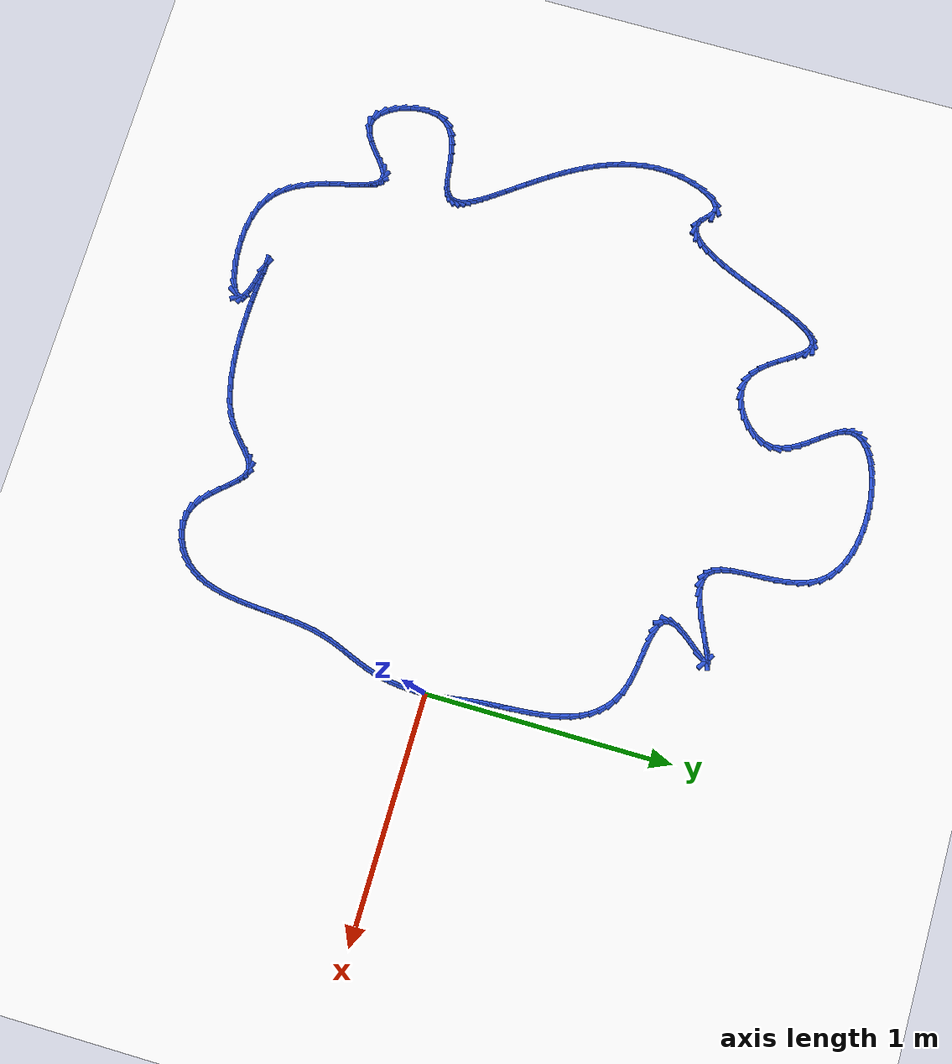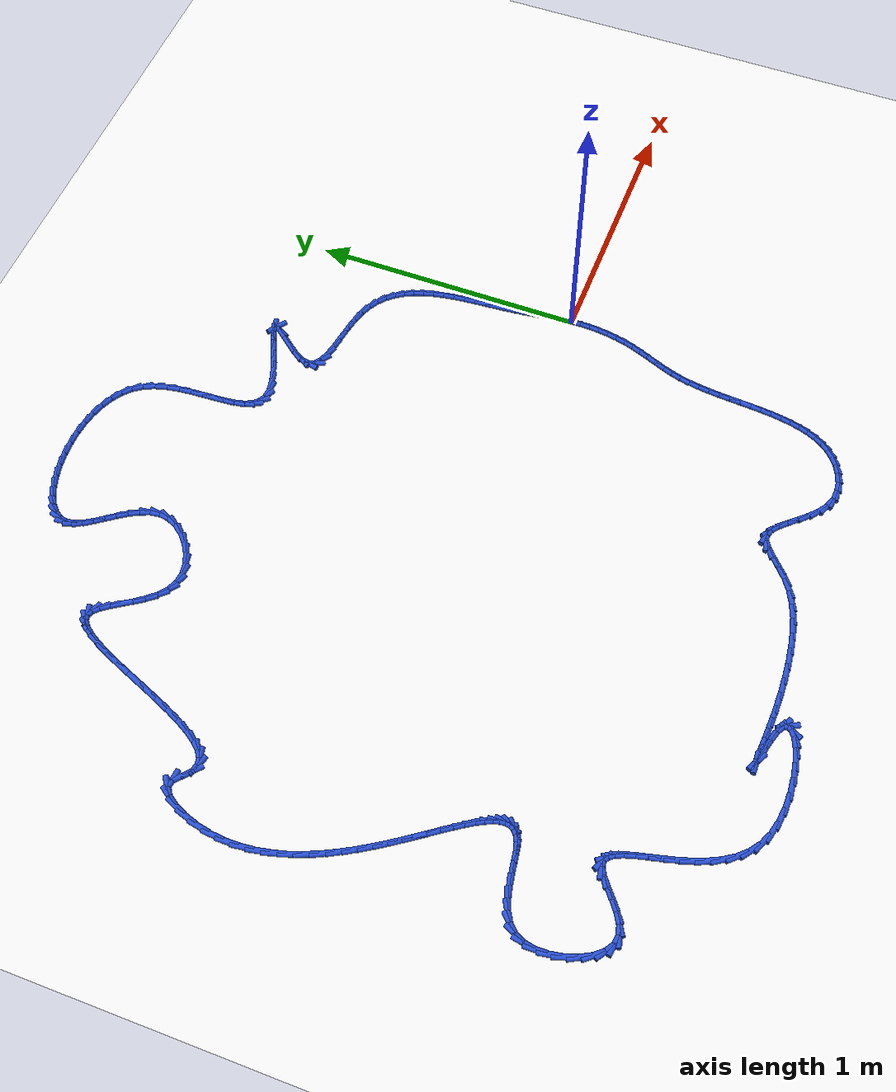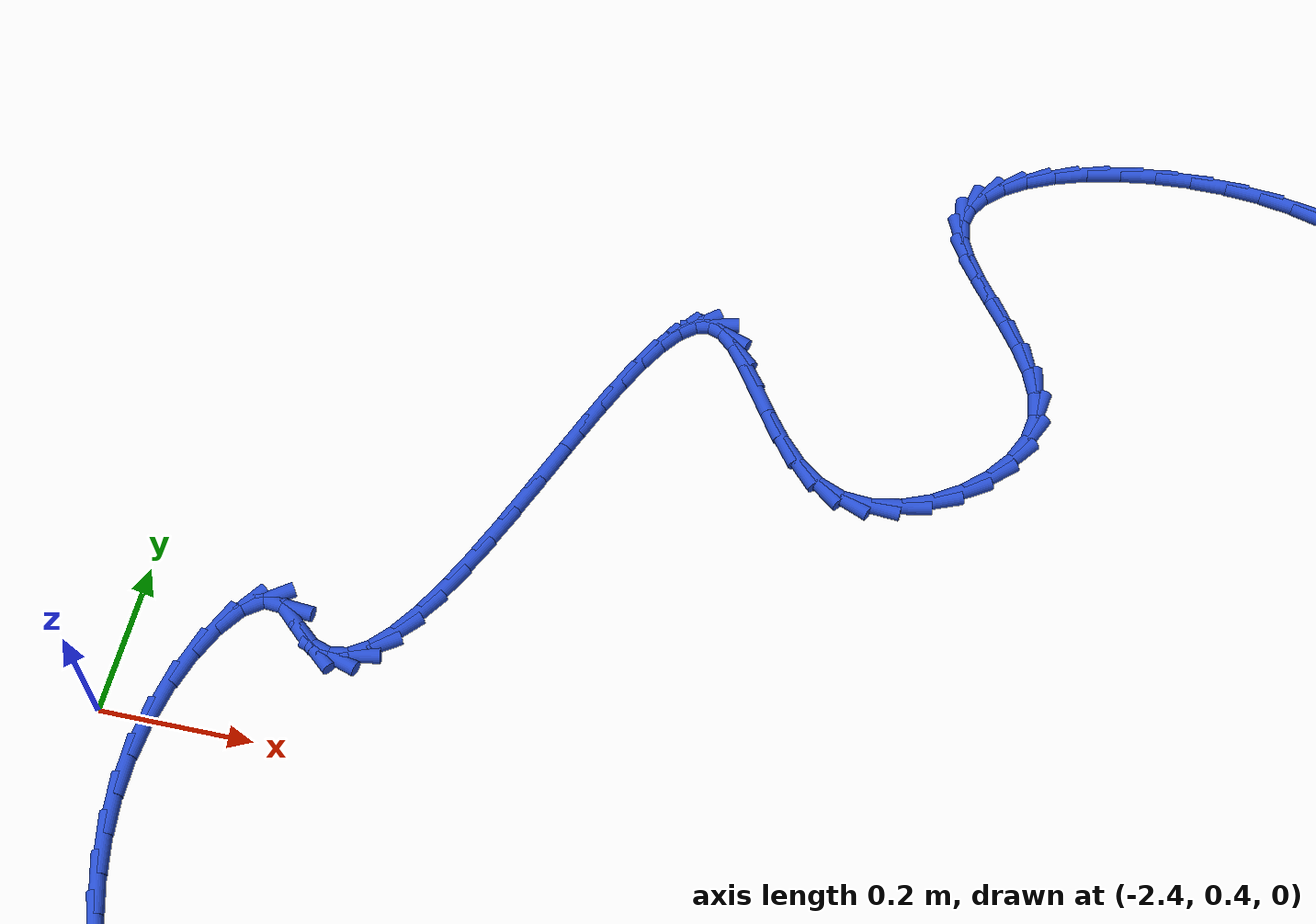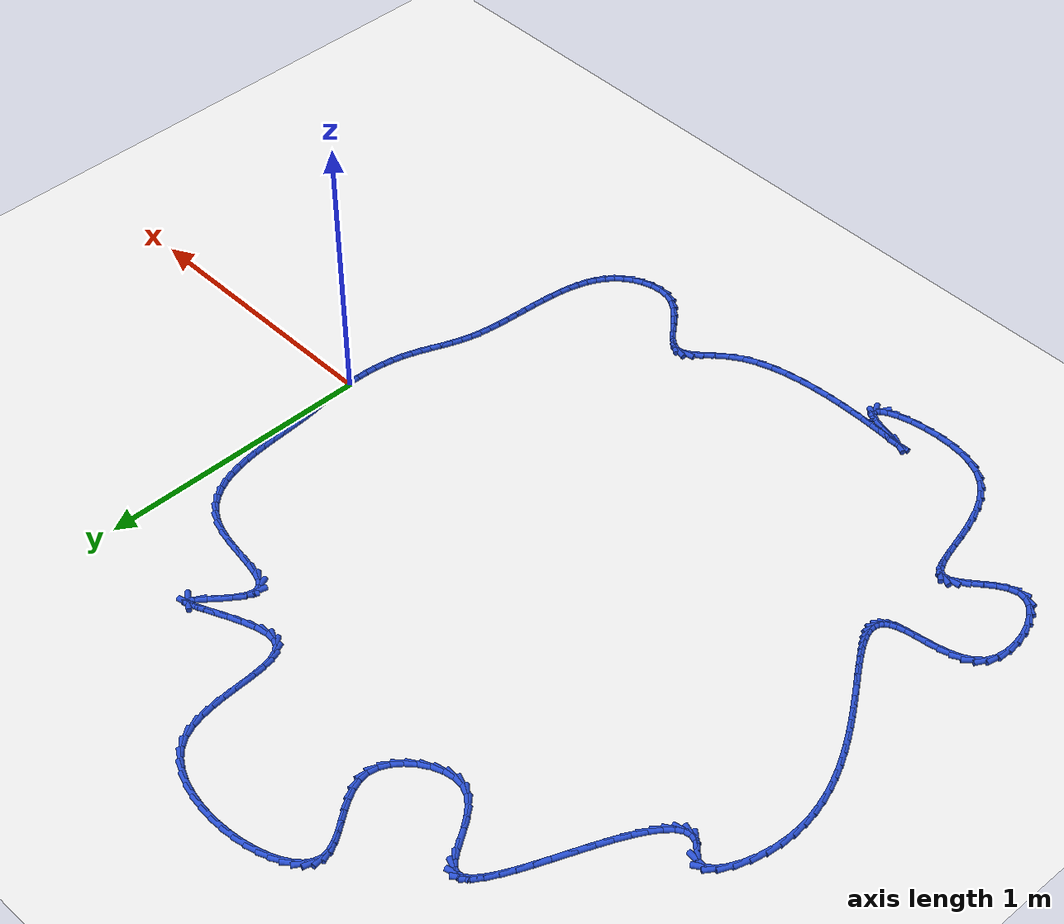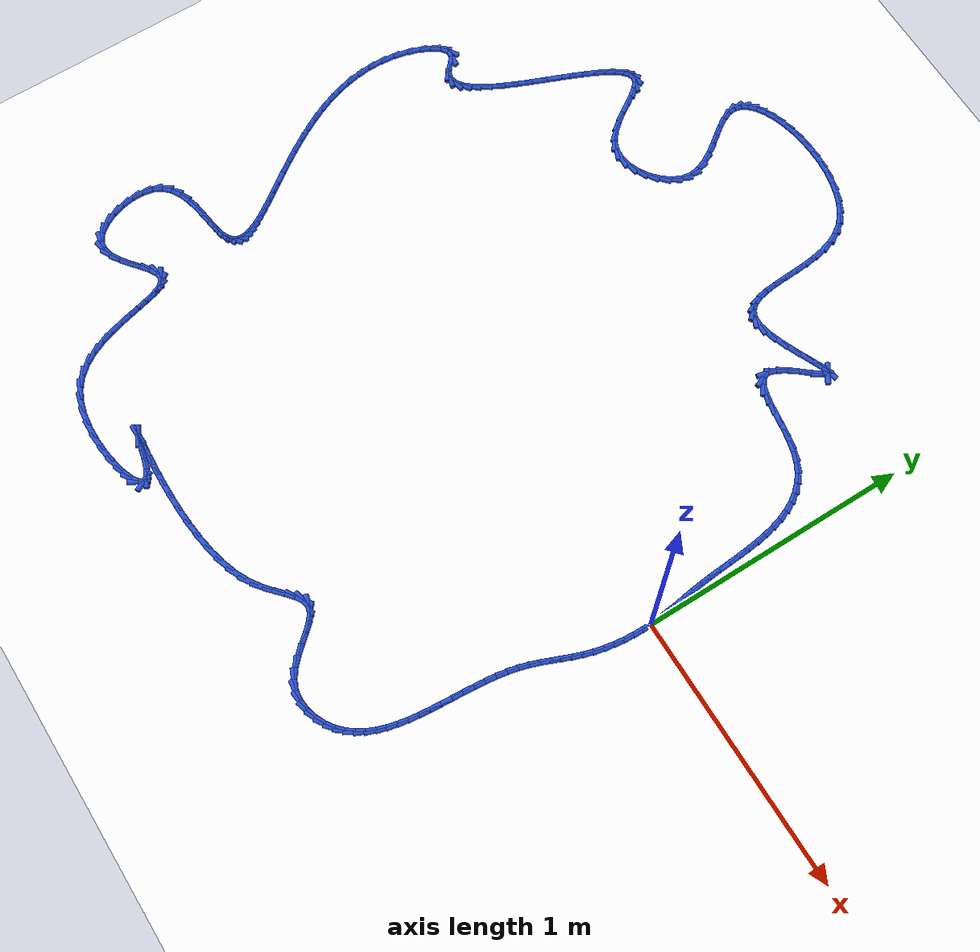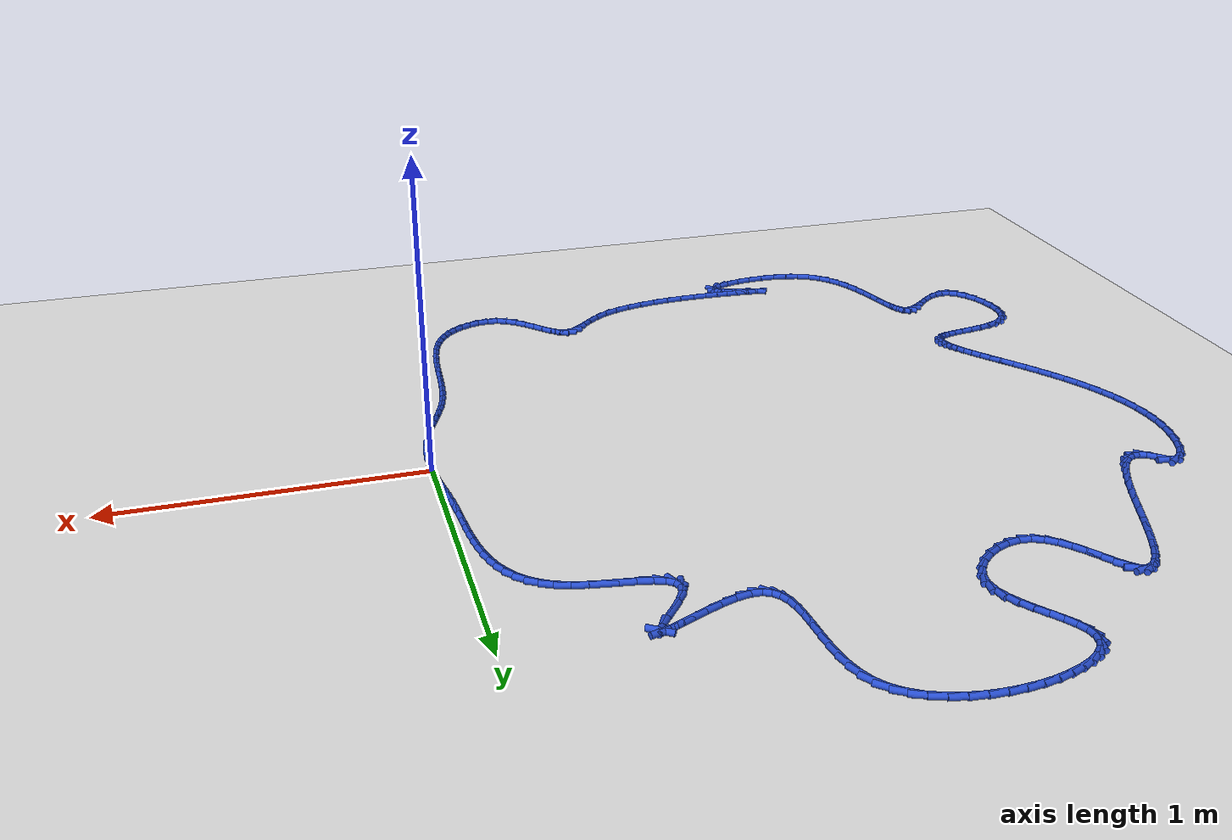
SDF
<sdf version="1.6">
 <world name="default">
  <light name="sun" type="directional">
   <pose>0 0 10 0 -0 0</pose>
   <diffuse>0.8 0.8 0.8 1</diffuse>
   <specular>0.2 0.2 0.2 1</specular>
   <attenuation>
    <range>1000</range>
    <constant>0.9</constant>
    <linear>0.01</linear>
    <quadratic>0.001</quadratic>
   </attenuation>
   <direction>-0.5 0.1 -0.9</direction>
  </light>
  <model name="ground_plane">
   <static>1</static>
   <link name="link">
    <collision name="collision">
     <geometry><plane><normal>0 0 1</normal><size>100 100</size></plane></geometry>
     <surface><friction><ode><mu>100</mu><mu2>50</mu2></ode></friction></surface>
    </collision>
    <visual name="visual">
     <cast_shadows>0</cast_shadows>
     <geometry><plane><normal>0 0 1</normal><size>100 100</size></plane></geometry>
     <material>
      <script><uri>file://media/materials/scripts/gazebo.material</uri><name>Gazebo/WhiteGlow</name></script>
     </material>
    </visual>
   </link>
  </model>
  <gravity>0 0 -9.8</gravity>
  <magnetic_field>6e-06 2.3e-05 -4.2e-05</magnetic_field>
  <atmosphere type="adiabatic"/>
  <physics name="default_physics" default="0" type="ode">
   <max_step_size>0.001</max_step_size>
   <real_time_factor>1</real_time_factor>
   <real_time_update_rate>1000</real_time_update_rate>
  </physics>
  <scene><ambient>0.4 0.4 0.4 1</ambient><background>0.7 0.7 0.7 1</background><shadows>1</shadows></scene>
  <spherical_coordinates>
   <surface_model>EARTH_WGS84</surface_model>
   <latitude_deg>0</latitude_deg>
   <longitude_deg>0</longitude_deg>
   <elevation>0</elevation>
   <heading_deg>0</heading_deg>
  </spherical_coordinates>
  <model name="line">
   <link name="link_0">
    <pose>-3.122502256758253e-17 8.326672684688674e-17 0.01 0 1.57 -1.5030407779389605</pose>
    <collision name="collision">
     <geometry><cylinder><radius>0.01</radius><length>0.08</length></cylinder></geometry>
    </collision>
    <visual name="visual">
     <material>
      <script><name>Gazebo/Blue</name><uri>file://media/materials/scripts/gazebo.material</uri></script>
     </material>
     <geometry><cylinder><radius>0.01</radius><length>0.08</length></cylinder></geometry>
    </visual>
   </link>
   <link name="link_1">
    <pose>-0.002415050710651432 0.03558902461273474 0.01 0 1.57 -1.4665003694563987</pose>
    <collision name="collision">
     <geometry><cylinder><radius>0.01</radius><length>0.08</length></cylinder></geometry>
    </collision>
    <visual name="visual">
     <material>
      <script><name>Gazebo/Blue</name><uri>file://media/materials/scripts/gazebo.material</uri></script>
     </material>
     <geometry><cylinder><radius>0.01</radius><length>0.08</length></cylinder></geometry>
    </visual>
   </link>
   <link name="link_2">
    <pose>-0.006111138607291392 0.07089889359107344 0.01 0 1.57 -1.442517594841231</pose>
    <collision name="collision">
     <geometry><cylinder><radius>0.01</radius><length>0.08</length></cylinder></geometry>
    </collision>
    <visual name="visual">
     <material>
      <script><name>Gazebo/Blue</name><uri>file://media/materials/scripts/gazebo.material</uri></script>
     </material>
     <geometry><cylinder><radius>0.01</radius><length>0.08</length></cylinder></geometry>
    </visual>
   </link>
   <link name="link_3">
    <pose>-0.01066798711388269 0.10622685483960265 0.01 0 1.57 -1.4315003370076975</pose>
    <collision name="collision">
     <geometry><cylinder><radius>0.01</radius><length>0.08</length></cylinder></geometry>
    </collision>
    <visual name="visual">
     <material>
      <script><name>Gazebo/Blue</name><uri>file://media/materials/scripts/gazebo.material</uri></script>
     </material>
     <geometry><cylinder><radius>0.01</radius><length>0.08</length></cylinder></geometry>
    </visual>
   </link>
   <link name="link_4">
    <pose>-0.015665319654388124 0.14187015626290891 0.01 0 1.57 -1.4332774170633384</pose>
    <collision name="collision">
     <geometry><cylinder><radius>0.01</radius><length>0.08</length></cylinder></geometry>
    </collision>
    <visual name="visual">
     <material>
      <script><name>Gazebo/Blue</name><uri>file://media/materials/scripts/gazebo.material</uri></script>
     </material>
     <geometry><cylinder><radius>0.01</radius><length>0.08</length></cylinder></geometry>
    </visual>
   </link>
   <link name="link_5">
    <pose>-0.020682859652770474 0.17812604576557875 0.01 0 1.57 -1.4471896794429266</pose>
    <collision name="collision">
     <geometry><cylinder><radius>0.01</radius><length>0.08</length></cylinder></geometry>
    </collision>
    <visual name="visual">
     <material>
      <script><name>Gazebo/Blue</name><uri>file://media/materials/scripts/gazebo.material</uri></script>
     </material>
     <geometry><cylinder><radius>0.01</radius><length>0.08</length></cylinder></geometry>
    </visual>
   </link>
   <link name="link_6">
    <pose>-0.02530033053299255 0.2152917712521987 0.01 0 1.57 -1.4713167224160402</pose>
    <collision name="collision">
     <geometry><cylinder><radius>0.01</radius><length>0.08</length></cylinder></geometry>
    </collision>
    <visual name="visual">
     <material>
      <script><name>Gazebo/Blue</name><uri>file://media/materials/scripts/gazebo.material</uri></script>
     </material>
     <geometry><cylinder><radius>0.01</radius><length>0.08</length></cylinder></geometry>
    </visual>
   </link>
   <link name="link_7">
    <pose>-0.0291279117036364 0.2536408046802877 0.01 0 1.57 -1.492112859820639</pose>
    <collision name="collision">
     <geometry><cylinder><radius>0.01</radius><length>0.08</length></cylinder></geometry>
    </collision>
    <visual name="visual">
     <material>
      <script><name>Gazebo/Blue</name><uri>file://media/materials/scripts/gazebo.material</uri></script>
     </material>
     <geometry><cylinder><radius>0.01</radius><length>0.08</length></cylinder></geometry>
    </visual>
   </link>
   <link name="link_8">
    <pose>-0.032238000089553284 0.2930857805779441 0.01 0 1.57 -1.500611982437879</pose>
    <collision name="collision">
     <geometry><cylinder><radius>0.01</radius><length>0.08</length></cylinder></geometry>
    </collision>
    <visual name="visual">
     <material>
      <script><name>Gazebo/Blue</name><uri>file://media/materials/scripts/gazebo.material</uri></script>
     </material>
     <geometry><cylinder><radius>0.01</radius><length>0.08</length></cylinder></geometry>
    </visual>
   </link>
   <link name="link_9">
    <pose>-0.03506216555849448 0.33325893942312346 0.01 0 1.57 -1.4974142484269624</pose>
    <collision name="collision">
     <geometry><cylinder><radius>0.01</radius><length>0.08</length></cylinder></geometry>
    </collision>
    <visual name="visual">
     <material>
      <script><name>Gazebo/Blue</name><uri>file://media/materials/scripts/gazebo.material</uri></script>
     </material>
     <geometry><cylinder><radius>0.01</radius><length>0.08</length></cylinder></geometry>
    </visual>
   </link>
   <link name="link_10">
    <pose>-0.03804141315734557 0.3737851559716594 0.01 0 1.57 -1.482753693875373</pose>
    <collision name="collision">
     <geometry><cylinder><radius>0.01</radius><length>0.08</length></cylinder></geometry>
    </collision>
    <visual name="visual">
     <material>
      <script><name>Gazebo/Blue</name><uri>file://media/materials/scripts/gazebo.material</uri></script>
     </material>
     <geometry><cylinder><radius>0.01</radius><length>0.08</length></cylinder></geometry>
    </visual>
   </link>
   <link name="link_11">
    <pose>-0.04161674793299211 0.4142893049793852 0.01 0 1.57 -1.4562961739968132</pose>
    <collision name="collision">
     <geometry><cylinder><radius>0.01</radius><length>0.08</length></cylinder></geometry>
    </collision>
    <visual name="visual">
     <material>
      <script><name>Gazebo/Blue</name><uri>file://media/materials/scripts/gazebo.material</uri></script>
     </material>
     <geometry><cylinder><radius>0.01</radius><length>0.08</length></cylinder></geometry>
    </visual>
   </link>
   <link name="link_12">
    <pose>-0.046229174932319594 0.45439626120213383 0.01 0 1.57 -1.4171775455345788</pose>
    <collision name="collision">
     <geometry><cylinder><radius>0.01</radius><length>0.08</length></cylinder></geometry>
    </collision>
    <visual name="visual">
     <material>
      <script><name>Gazebo/Blue</name><uri>file://media/materials/scripts/gazebo.material</uri></script>
     </material>
     <geometry><cylinder><radius>0.01</radius><length>0.08</length></cylinder></geometry>
    </visual>
   </link>
   <link name="link_13">
    <pose>-0.052319699202213604 0.493730899395739 0.01 0 1.57 -1.364047035410262</pose>
    <collision name="collision">
     <geometry><cylinder><radius>0.01</radius><length>0.08</length></cylinder></geometry>
    </collision>
    <visual name="visual">
     <material>
      <script><name>Gazebo/Blue</name><uri>file://media/materials/scripts/gazebo.material</uri></script>
     </material>
     <geometry><cylinder><radius>0.01</radius><length>0.08</length></cylinder></geometry>
    </visual>
   </link>
   <link name="link_14">
    <pose>-0.06032932578955969 0.531918094316034 0.01 0 1.57 -1.295168387860842</pose>
    <collision name="collision">
     <geometry><cylinder><radius>0.01</radius><length>0.08</length></cylinder></geometry>
    </collision>
    <visual name="visual">
     <material>
      <script><name>Gazebo/Blue</name><uri>file://media/materials/scripts/gazebo.material</uri></script>
     </material>
     <geometry><cylinder><radius>0.01</radius><length>0.08</length></cylinder></geometry>
    </visual>
   </link>
   <link name="link_15">
    <pose>-0.0706990597412434 0.5685827207188522 0.01 0 1.57 -1.2086698382049734</pose>
    <collision name="collision">
     <geometry><cylinder><radius>0.01</radius><length>0.08</length></cylinder></geometry>
    </collision>
    <visual name="visual">
     <material>
      <script><name>Gazebo/Blue</name><uri>file://media/materials/scripts/gazebo.material</uri></script>
     </material>
     <geometry><cylinder><radius>0.01</radius><length>0.08</length></cylinder></geometry>
    </visual>
   </link>
   <link name="link_16">
    <pose>-0.08386990610415024 0.6033496533600268 0.01 0 1.57 -1.1030724608693272</pose>
    <collision name="collision">
     <geometry><cylinder><radius>0.01</radius><length>0.08</length></cylinder></geometry>
    </collision>
    <visual name="visual">
     <material>
      <script><name>Gazebo/Blue</name><uri>file://media/materials/scripts/gazebo.material</uri></script>
     </material>
     <geometry><cylinder><radius>0.01</radius><length>0.08</length></cylinder></geometry>
    </visual>
   </link>
   <link name="link_17">
    <pose>-0.10028286992516583 0.6358437669953914 0.01 0 1.57 -0.9782002376338371</pose>
    <collision name="collision">
     <geometry><cylinder><radius>0.01</radius><length>0.08</length></cylinder></geometry>
    </collision>
    <visual name="visual">
     <material>
      <script><name>Gazebo/Blue</name><uri>file://media/materials/scripts/gazebo.material</uri></script>
     </material>
     <geometry><cylinder><radius>0.01</radius><length>0.08</length></cylinder></geometry>
    </visual>
   </link>
   <link name="link_18">
    <pose>-0.12037895625117563 0.665689936380779 0.01 0 1.57 -0.8363477039472466</pose>
    <collision name="collision">
     <geometry><cylinder><radius>0.01</radius><length>0.08</length></cylinder></geometry>
    </collision>
    <visual name="visual">
     <material>
      <script><name>Gazebo/Blue</name><uri>file://media/materials/scripts/gazebo.material</uri></script>
     </material>
     <geometry><cylinder><radius>0.01</radius><length>0.08</length></cylinder></geometry>
    </visual>
   </link>
   <link name="link_19">
    <pose>-0.1445991701290653 0.6925130362720234 0.01 0 1.57 -0.6830863710594951</pose>
    <collision name="collision">
     <geometry><cylinder><radius>0.01</radius><length>0.08</length></cylinder></geometry>
    </collision>
    <visual name="visual">
     <material>
      <script><name>Gazebo/Blue</name><uri>file://media/materials/scripts/gazebo.material</uri></script>
     </material>
     <geometry><cylinder><radius>0.01</radius><length>0.08</length></cylinder></geometry>
    </visual>
   </link>
   <link name="link_20">
    <pose>-0.17338451660572024 0.7159379414249577 0.01 0 1.57 -0.5267461093109288</pose>
    <collision name="collision">
     <geometry><cylinder><radius>0.01</radius><length>0.08</length></cylinder></geometry>
    </collision>
    <visual name="visual">
     <material>
      <script><name>Gazebo/Blue</name><uri>file://media/materials/scripts/gazebo.material</uri></script>
     </material>
     <geometry><cylinder><radius>0.01</radius><length>0.08</length></cylinder></geometry>
    </visual>
   </link>
   <link name="link_21">
    <pose>-0.20717600072802617 0.7355895265954151 0.01 0 1.57 -0.3762813209090379</pose>
    <collision name="collision">
     <geometry><cylinder><radius>0.01</radius><length>0.08</length></cylinder></geometry>
    </collision>
    <visual name="visual">
     <material>
      <script><name>Gazebo/Blue</name><uri>file://media/materials/scripts/gazebo.material</uri></script>
     </material>
     <geometry><cylinder><radius>0.01</radius><length>0.08</length></cylinder></geometry>
    </visual>
   </link>
   <link name="link_22">
    <pose>-0.24641429832178813 0.7510928594967353 0.01 0 1.57 -0.2504060085251132</pose>
    <collision name="collision">
     <geometry><cylinder><radius>0.01</radius><length>0.08</length></cylinder></geometry>
    </collision>
    <visual name="visual">
     <material>
      <script><name>Gazebo/Blue</name><uri>file://media/materials/scripts/gazebo.material</uri></script>
     </material>
     <geometry><cylinder><radius>0.01</radius><length>0.08</length></cylinder></geometry>
    </visual>
   </link>
   <link name="link_23">
    <pose>-0.2908726784310996 0.7624641770464414 0.01 0 1.57 -0.17683478753055085</pose>
    <collision name="collision">
     <geometry><cylinder><radius>0.01</radius><length>0.08</length></cylinder></geometry>
    </collision>
    <visual name="visual">
     <material>
      <script><name>Gazebo/Blue</name><uri>file://media/materials/scripts/gazebo.material</uri></script>
     </material>
     <geometry><cylinder><radius>0.01</radius><length>0.08</length></cylinder></geometry>
    </visual>
   </link>
   <link name="link_24">
    <pose>-0.3382564914490906 0.7709317297573361 0.01 0 1.57 -0.14650194255312052</pose>
    <collision name="collision">
     <geometry><cylinder><radius>0.01</radius><length>0.08</length></cylinder></geometry>
    </collision>
    <visual name="visual">
     <material>
      <script><name>Gazebo/Blue</name><uri>file://media/materials/scripts/gazebo.material</uri></script>
     </material>
     <geometry><cylinder><radius>0.01</radius><length>0.08</length></cylinder></geometry>
    </visual>
   </link>
   <link name="link_25">
    <pose>-0.3858717842939554 0.7779578011589641 0.01 0 1.57 -0.15481828259234995</pose>
    <collision name="collision">
     <geometry><cylinder><radius>0.01</radius><length>0.08</length></cylinder></geometry>
    </collision>
    <visual name="visual">
     <material>
      <script><name>Gazebo/Blue</name><uri>file://media/materials/scripts/gazebo.material</uri></script>
     </material>
     <geometry><cylinder><radius>0.01</radius><length>0.08</length></cylinder></geometry>
    </visual>
   </link>
   <link name="link_26">
    <pose>-0.43102460388388847 0.7850046747808693 0.01 0 1.57 -0.21012030153353362</pose>
    <collision name="collision">
     <geometry><cylinder><radius>0.01</radius><length>0.08</length></cylinder></geometry>
    </collision>
    <visual name="visual">
     <material>
      <script><name>Gazebo/Blue</name><uri>file://media/materials/scripts/gazebo.material</uri></script>
     </material>
     <geometry><cylinder><radius>0.01</radius><length>0.08</length></cylinder></geometry>
    </visual>
   </link>
   <link name="link_27">
    <pose>-0.47102099713708523 0.7935346341525976 0.01 0 1.57 -0.3428752116892714</pose>
    <collision name="collision">
     <geometry><cylinder><radius>0.01</radius><length>0.08</length></cylinder></geometry>
    </collision>
    <visual name="visual">
     <material>
      <script><name>Gazebo/Blue</name><uri>file://media/materials/scripts/gazebo.material</uri></script>
     </material>
     <geometry><cylinder><radius>0.01</radius><length>0.08</length></cylinder></geometry>
    </visual>
   </link>
   <link name="link_28">
    <pose>-0.5031670109717399 0.8050099628036931 0.01 0 1.57 -0.6340044579413768</pose>
    <collision name="collision">
     <geometry><cylinder><radius>0.01</radius><length>0.08</length></cylinder></geometry>
    </collision>
    <visual name="visual">
     <material>
      <script><name>Gazebo/Blue</name><uri>file://media/materials/scripts/gazebo.material</uri></script>
     </material>
     <geometry><cylinder><radius>0.01</radius><length>0.08</length></cylinder></geometry>
    </visual>
   </link>
   <link name="link_29">
    <pose>-0.5247686923060474 0.8208929442637007 0.01 0 1.57 -1.203747088177911</pose>
    <collision name="collision">
     <geometry><cylinder><radius>0.01</radius><length>0.08</length></cylinder></geometry>
    </collision>
    <visual name="visual">
     <material>
      <script><name>Gazebo/Blue</name><uri>file://media/materials/scripts/gazebo.material</uri></script>
     </material>
     <geometry><cylinder><radius>0.01</radius><length>0.08</length></cylinder></geometry>
    </visual>
   </link>
   <link name="link_30">
    <pose>-0.5331320880582021 0.842645862062165 0.01 0 1.57 1.3257189093136208</pose>
    <collision name="collision">
     <geometry><cylinder><radius>0.01</radius><length>0.08</length></cylinder></geometry>
    </collision>
    <visual name="visual">
     <material>
      <script><name>Gazebo/Blue</name><uri>file://media/materials/scripts/gazebo.material</uri></script>
     </material>
     <geometry><cylinder><radius>0.01</radius><length>0.08</length></cylinder></geometry>
    </visual>
   </link>
   <link name="link_31">
    <pose>-0.5259093899618574 0.8715245335963622 0.01 0 1.57 1.0380452789056749</pose>
    <collision name="collision">
     <geometry><cylinder><radius>0.01</radius><length>0.08</length></cylinder></geometry>
    </collision>
    <visual name="visual">
     <material>
      <script><name>Gazebo/Blue</name><uri>file://media/materials/scripts/gazebo.material</uri></script>
     </material>
     <geometry><cylinder><radius>0.01</radius><length>0.08</length></cylinder></geometry>
    </visual>
   </link>
   <link name="link_32">
    <pose>-0.5056690816337313 0.90585233953516 0.01 0 1.57 0.925611569834618</pose>
    <collision name="collision">
     <geometry><cylinder><radius>0.01</radius><length>0.08</length></cylinder></geometry>
    </collision>
    <visual name="visual">
     <material>
      <script><name>Gazebo/Blue</name><uri>file://media/materials/scripts/gazebo.material</uri></script>
     </material>
     <geometry><cylinder><radius>0.01</radius><length>0.08</length></cylinder></geometry>
    </visual>
   </link>
   <link name="link_33">
    <pose>-0.4786340327649526 0.9417729169115141 0.01 0 1.57 0.8846221475491244</pose>
    <collision name="collision">
     <geometry><cylinder><radius>0.01</radius><length>0.08</length></cylinder></geometry>
    </collision>
    <visual name="visual">
     <material>
      <script><name>Gazebo/Blue</name><uri>file://media/materials/scripts/gazebo.material</uri></script>
     </material>
     <geometry><cylinder><radius>0.01</radius><length>0.08</length></cylinder></geometry>
    </visual>
   </link>
   <link name="link_34">
    <pose>-0.451113894973161 0.975378139658323 0.01 0 1.57 0.9007452691590183</pose>
    <collision name="collision">
     <geometry><cylinder><radius>0.01</radius><length>0.08</length></cylinder></geometry>
    </collision>
    <visual name="visual">
     <material>
      <script><name>Gazebo/Blue</name><uri>file://media/materials/scripts/gazebo.material</uri></script>
     </material>
     <geometry><cylinder><radius>0.01</radius><length>0.08</length></cylinder></geometry>
    </visual>
   </link>
   <link name="link_35">
    <pose>-0.42941831987599555 1.0027598817084835 0.01 0 1.57 1.0646485575879678</pose>
    <collision name="collision">
     <geometry><cylinder><radius>0.01</radius><length>0.08</length></cylinder></geometry>
    </collision>
    <visual name="visual">
     <material>
      <script><name>Gazebo/Blue</name><uri>file://media/materials/scripts/gazebo.material</uri></script>
     </material>
     <geometry><cylinder><radius>0.01</radius><length>0.08</length></cylinder></geometry>
    </visual>
   </link>
   <link name="link_36">
    <pose>-0.41985596835057004 1.020010727504872 0.01 0 1.57 -0.5976320957336914</pose>
    <collision name="collision">
     <geometry><cylinder><radius>0.01</radius><length>0.08</length></cylinder></geometry>
    </collision>
    <visual name="visual">
     <material>
      <script><name>Gazebo/Blue</name><uri>file://media/materials/scripts/gazebo.material</uri></script>
     </material>
     <geometry><cylinder><radius>0.01</radius><length>0.08</length></cylinder></geometry>
    </visual>
   </link>
   <link name="link_37">
    <pose>-0.4267098677380078 1.0246759454191865 0.01 0 1.57 0.2692749755799874</pose>
    <collision name="collision">
     <geometry><cylinder><radius>0.01</radius><length>0.08</length></cylinder></geometry>
    </collision>
    <visual name="visual">
     <material>
      <script><name>Gazebo/Blue</name><uri>file://media/materials/scripts/gazebo.material</uri></script>
     </material>
     <geometry><cylinder><radius>0.01</radius><length>0.08</length></cylinder></geometry>
    </visual>
   </link>
   <link name="link_38">
    <pose>-0.4479818811574569 1.0188053433449307 0.01 0 1.57 0.3935718560412883</pose>
    <collision name="collision">
     <geometry><cylinder><radius>0.01</radius><length>0.08</length></cylinder></geometry>
    </collision>
    <visual name="visual">
     <material>
      <script><name>Gazebo/Blue</name><uri>file://media/materials/scripts/gazebo.material</uri></script>
     </material>
     <geometry><cylinder><radius>0.01</radius><length>0.08</length></cylinder></geometry>
    </visual>
   </link>
   <link name="link_39">
    <pose>-0.480460043892404 1.0053192263104016 0.01 0 1.57 0.422212059788577</pose>
    <collision name="collision">
     <geometry><cylinder><radius>0.01</radius><length>0.08</length></cylinder></geometry>
    </collision>
    <visual name="visual">
     <material>
      <script><name>Gazebo/Blue</name><uri>file://media/materials/scripts/gazebo.material</uri></script>
     </material>
     <geometry><cylinder><radius>0.01</radius><length>0.08</length></cylinder></geometry>
    </visual>
   </link>
   <link name="link_40">
    <pose>-0.5209323912263357 0.9871378993438962 0.01 0 1.57 0.4153252706616437</pose>
    <collision name="collision">
     <geometry><cylinder><radius>0.01</radius><length>0.08</length></cylinder></geometry>
    </collision>
    <visual name="visual">
     <material>
      <script><name>Gazebo/Blue</name><uri>file://media/materials/scripts/gazebo.material</uri></script>
     </material>
     <geometry><cylinder><radius>0.01</radius><length>0.08</length></cylinder></geometry>
    </visual>
   </link>
   <link name="link_41">
    <pose>-0.5661869584427399 0.9671816674737121 0.01 0 1.57 0.38199495099625697</pose>
    <collision name="collision">
     <geometry><cylinder><radius>0.01</radius><length>0.08</length></cylinder></geometry>
    </collision>
    <visual name="visual">
     <material>
      <script><name>Gazebo/Blue</name><uri>file://media/materials/scripts/gazebo.material</uri></script>
     </material>
     <geometry><cylinder><radius>0.01</radius><length>0.08</length></cylinder></geometry>
    </visual>
   </link>
   <link name="link_42">
    <pose>-0.6130117808251029 0.9483708357281462 0.01 0 1.57 0.3154447966175286</pose>
    <collision name="collision">
     <geometry><cylinder><radius>0.01</radius><length>0.08</length></cylinder></geometry>
    </collision>
    <visual name="visual">
     <material>
      <script><name>Gazebo/Blue</name><uri>file://media/materials/scripts/gazebo.material</uri></script>
     </material>
     <geometry><cylinder><radius>0.01</radius><length>0.08</length></cylinder></geometry>
    </visual>
   </link>
   <link name="link_43">
    <pose>-0.6581948936569116 0.9336257091354958 0.01 0 1.57 0.19007090434024412</pose>
    <collision name="collision">
     <geometry><cylinder><radius>0.01</radius><length>0.08</length></cylinder></geometry>
    </collision>
    <visual name="visual">
     <material>
      <script><name>Gazebo/Blue</name><uri>file://media/materials/scripts/gazebo.material</uri></script>
     </material>
     <geometry><cylinder><radius>0.01</radius><length>0.08</length></cylinder></geometry>
    </visual>
   </link>
   <link name="link_44">
    <pose>-0.6985243322216529 0.9258665927240581 0.01 0 1.57 -0.05773627390485298</pose>
    <collision name="collision">
     <geometry><cylinder><radius>0.01</radius><length>0.08</length></cylinder></geometry>
    </collision>
    <visual name="visual">
     <material>
      <script><name>Gazebo/Blue</name><uri>file://media/materials/scripts/gazebo.material</uri></script>
     </material>
     <geometry><cylinder><radius>0.01</radius><length>0.08</length></cylinder></geometry>
    </visual>
   </link>
   <link name="link_45">
    <pose>-0.7310731593778234 0.9277479316556336 0.01 0 1.57 -0.44436669307397236</pose>
    <collision name="collision">
     <geometry><cylinder><radius>0.01</radius><length>0.08</length></cylinder></geometry>
    </collision>
    <visual name="visual">
     <material>
      <script><name>Gazebo/Blue</name><uri>file://media/materials/scripts/gazebo.material</uri></script>
     </material>
     <geometry><cylinder><radius>0.01</radius><length>0.08</length></cylinder></geometry>
    </visual>
   </link>
   <link name="link_46">
    <pose>-0.7555953224692225 0.9394235723645725 0.01 0 1.57 -0.8520096115226901</pose>
    <collision name="collision">
     <geometry><cylinder><radius>0.01</radius><length>0.08</length></cylinder></geometry>
    </collision>
    <visual name="visual">
     <material>
      <script><name>Gazebo/Blue</name><uri>file://media/materials/scripts/gazebo.material</uri></script>
     </material>
     <geometry><cylinder><radius>0.01</radius><length>0.08</length></cylinder></geometry>
    </visual>
   </link>
   <link name="link_47">
    <pose>-0.7733148072370445 0.9596761809281527 0.01 0 1.57 -1.155904057189359</pose>
    <collision name="collision">
     <geometry><cylinder><radius>0.01</radius><length>0.08</length></cylinder></geometry>
    </collision>
    <visual name="visual">
     <material>
      <script><name>Gazebo/Blue</name><uri>file://media/materials/scripts/gazebo.material</uri></script>
     </material>
     <geometry><cylinder><radius>0.01</radius><length>0.08</length></cylinder></geometry>
    </visual>
   </link>
   <link name="link_48">
    <pose>-0.7854706957549521 0.9872743422985744 0.01 0 1.57 -1.3425443921107674</pose>
    <collision name="collision">
     <geometry><cylinder><radius>0.01</radius><length>0.08</length></cylinder></geometry>
    </collision>
    <visual name="visual">
     <material>
      <script><name>Gazebo/Blue</name><uri>file://media/materials/scripts/gazebo.material</uri></script>
     </material>
     <geometry><cylinder><radius>0.01</radius><length>0.08</length></cylinder></geometry>
    </visual>
   </link>
   <link name="link_49">
    <pose>-0.7933020700966062 1.020986641428037 0.01 0 1.57 -1.4484428341530156</pose>
    <collision name="collision">
     <geometry><cylinder><radius>0.01</radius><length>0.08</length></cylinder></geometry>
    </collision>
    <visual name="visual">
     <material>
      <script><name>Gazebo/Blue</name><uri>file://media/materials/scripts/gazebo.material</uri></script>
     </material>
     <geometry><cylinder><radius>0.01</radius><length>0.08</length></cylinder></geometry>
    </visual>
   </link>
   <link name="link_50">
    <pose>-0.7980480123356694 1.059581663268741 0.01 0 1.57 -1.5022684351505027</pose>
    <collision name="collision">
     <geometry><cylinder><radius>0.01</radius><length>0.08</length></cylinder></geometry>
    </collision>
    <visual name="visual">
     <material>
      <script><name>Gazebo/Blue</name><uri>file://media/materials/scripts/gazebo.material</uri></script>
     </material>
     <geometry><cylinder><radius>0.01</radius><length>0.08</length></cylinder></geometry>
    </visual>
   </link>
   <link name="link_51">
    <pose>-0.8009476045458033 1.101827992772886 0.01 0 1.57 -1.5195201103953446</pose>
    <collision name="collision">
     <geometry><cylinder><radius>0.01</radius><length>0.08</length></cylinder></geometry>
    </collision>
    <visual name="visual">
     <material>
      <script><name>Gazebo/Blue</name><uri>file://media/materials/scripts/gazebo.material</uri></script>
     </material>
     <geometry><cylinder><radius>0.01</radius><length>0.08</length></cylinder></geometry>
    </visual>
   </link>
   <link name="link_52">
    <pose>-0.8032399288006696 1.1464942148926724 0.01 0 1.57 -1.5071129028551404</pose>
    <collision name="collision">
     <geometry><cylinder><radius>0.01</radius><length>0.08</length></cylinder></geometry>
    </collision>
    <visual name="visual">
     <material>
      <script><name>Gazebo/Blue</name><uri>file://media/materials/scripts/gazebo.material</uri></script>
     </material>
     <geometry><cylinder><radius>0.01</radius><length>0.08</length></cylinder></geometry>
    </visual>
   </link>
   <link name="link_53">
    <pose>-0.806164067173931 1.1923489145803001 0.01 0 1.57 -1.4665078649283287</pose>
    <collision name="collision">
     <geometry><cylinder><radius>0.01</radius><length>0.08</length></cylinder></geometry>
    </collision>
    <visual name="visual">
     <material>
      <script><name>Gazebo/Blue</name><uri>file://media/materials/scripts/gazebo.material</uri></script>
     </material>
     <geometry><cylinder><radius>0.01</radius><length>0.08</length></cylinder></geometry>
    </visual>
   </link>
   <link name="link_54">
    <pose>-0.8109591017392487 1.238160676787969 0.01 0 1.57 -1.3951341965035355</pose>
    <collision name="collision">
     <geometry><cylinder><radius>0.01</radius><length>0.08</length></cylinder></geometry>
    </collision>
    <visual name="visual">
     <material>
      <script><name>Gazebo/Blue</name><uri>file://media/materials/scripts/gazebo.material</uri></script>
     </material>
     <geometry><cylinder><radius>0.01</radius><length>0.08</length></cylinder></geometry>
    </visual>
   </link>
   <link name="link_55">
    <pose>-0.8188641145702844 1.2826980864678788 0.01 0 1.57 -1.2871152686169394</pose>
    <collision name="collision">
     <geometry><cylinder><radius>0.01</radius><length>0.08</length></cylinder></geometry>
    </collision>
    <visual name="visual">
     <material>
      <script><name>Gazebo/Blue</name><uri>file://media/materials/scripts/gazebo.material</uri></script>
     </material>
     <geometry><cylinder><radius>0.01</radius><length>0.08</length></cylinder></geometry>
    </visual>
   </link>
   <link name="link_56">
    <pose>-0.8311181877407007 1.32472972857223 0.01 0 1.57 -1.1347811718032945</pose>
    <collision name="collision">
     <geometry><cylinder><radius>0.01</radius><length>0.08</length></cylinder></geometry>
    </collision>
    <visual name="visual">
     <material>
      <script><name>Gazebo/Blue</name><uri>file://media/materials/scripts/gazebo.material</uri></script>
     </material>
     <geometry><cylinder><radius>0.01</radius><length>0.08</length></cylinder></geometry>
    </visual>
   </link>
   <link name="link_57">
    <pose>-0.8489604033241588 1.3630241880532217 0.01 0 1.57 -0.9354595386576153</pose>
    <collision name="collision">
     <geometry><cylinder><radius>0.01</radius><length>0.08</length></cylinder></geometry>
    </collision>
    <visual name="visual">
     <material>
      <script><name>Gazebo/Blue</name><uri>file://media/materials/scripts/gazebo.material</uri></script>
     </material>
     <geometry><cylinder><radius>0.01</radius><length>0.08</length></cylinder></geometry>
    </visual>
   </link>
   <link name="link_58">
    <pose>-0.8735633219997162 1.3963921944097935 0.01 0 1.57 -0.7289780125217971</pose>
    <collision name="collision">
     <geometry><cylinder><radius>0.01</radius><length>0.08</length></cylinder></geometry>
    </collision>
    <visual name="visual">
     <material>
      <script><name>Gazebo/Blue</name><uri>file://media/materials/scripts/gazebo.material</uri></script>
     </material>
     <geometry><cylinder><radius>0.01</radius><length>0.08</length></cylinder></geometry>
    </visual>
   </link>
   <link name="link_59">
    <pose>-0.9049171007624246 1.4243935875228912 0.01 0 1.57 -0.5520698152929532</pose>
    <collision name="collision">
     <geometry><cylinder><radius>0.01</radius><length>0.08</length></cylinder></geometry>
    </collision>
    <visual name="visual">
     <material>
      <script><name>Gazebo/Blue</name><uri>file://media/materials/scripts/gazebo.material</uri></script>
     </material>
     <geometry><cylinder><radius>0.01</radius><length>0.08</length></cylinder></geometry>
    </visual>
   </link>
   <link name="link_60">
    <pose>-0.941995394731718 1.4472322107713014 0.01 0 1.57 -0.4051074546597271</pose>
    <collision name="collision">
     <geometry><cylinder><radius>0.01</radius><length>0.08</length></cylinder></geometry>
    </collision>
    <visual name="visual">
     <material>
      <script><name>Gazebo/Blue</name><uri>file://media/materials/scripts/gazebo.material</uri></script>
     </material>
     <geometry><cylinder><radius>0.01</radius><length>0.08</length></cylinder></geometry>
    </visual>
   </link>
   <link name="link_61">
    <pose>-0.9837387559082431 1.4651328799735053 0.01 0 1.57 -0.2829961685948971</pose>
    <collision name="collision">
     <geometry><cylinder><radius>0.01</radius><length>0.08</length></cylinder></geometry>
    </collision>
    <visual name="visual">
     <material>
      <script><name>Gazebo/Blue</name><uri>file://media/materials/scripts/gazebo.material</uri></script>
     </material>
     <geometry><cylinder><radius>0.01</radius><length>0.08</length></cylinder></geometry>
    </visual>
   </link>
   <link name="link_62">
    <pose>-1.0290877362926467 1.4783204109479866 0.01 0 1.57 -0.17967157997380753</pose>
    <collision name="collision">
     <geometry><cylinder><radius>0.01</radius><length>0.08</length></cylinder></geometry>
    </collision>
    <visual name="visual">
     <material>
      <script><name>Gazebo/Blue</name><uri>file://media/materials/scripts/gazebo.material</uri></script>
     </material>
     <geometry><cylinder><radius>0.01</radius><length>0.08</length></cylinder></geometry>
    </visual>
   </link>
   <link name="link_63">
    <pose>-1.0769828878855763 1.487019619513228 0.01 0 1.57 -0.08958407679733345</pose>
    <collision name="collision">
     <geometry><cylinder><radius>0.01</radius><length>0.08</length></cylinder></geometry>
    </collision>
    <visual name="visual">
     <material>
      <script><name>Gazebo/Blue</name><uri>file://media/materials/scripts/gazebo.material</uri></script>
     </material>
     <geometry><cylinder><radius>0.01</radius><length>0.08</length></cylinder></geometry>
    </visual>
   </link>
   <link name="link_64">
    <pose>-1.1263647626876787 1.4914553214877107 0.01 0 1.57 -0.0079704792170866</pose>
    <collision name="collision">
     <geometry><cylinder><radius>0.01</radius><length>0.08</length></cylinder></geometry>
    </collision>
    <visual name="visual">
     <material>
      <script><name>Gazebo/Blue</name><uri>file://media/materials/scripts/gazebo.material</uri></script>
     </material>
     <geometry><cylinder><radius>0.01</radius><length>0.08</length></cylinder></geometry>
    </visual>
   </link>
   <link name="link_65">
    <pose>-1.1761739126996007 1.4918523326899176 0.01 0 1.57 0.06936947722427453</pose>
    <collision name="collision">
     <geometry><cylinder><radius>0.01</radius><length>0.08</length></cylinder></geometry>
    </collision>
    <visual name="visual">
     <material>
      <script><name>Gazebo/Blue</name><uri>file://media/materials/scripts/gazebo.material</uri></script>
     </material>
     <geometry><cylinder><radius>0.01</radius><length>0.08</length></cylinder></geometry>
    </visual>
   </link>
   <link name="link_66">
    <pose>-1.2253508899219894 1.4884354689383312 0.01 0 1.57 0.14648184305750958</pose>
    <collision name="collision">
     <geometry><cylinder><radius>0.01</radius><length>0.08</length></cylinder></geometry>
    </collision>
    <visual name="visual">
     <material>
      <script><name>Gazebo/Blue</name><uri>file://media/materials/scripts/gazebo.material</uri></script>
     </material>
     <geometry><cylinder><radius>0.01</radius><length>0.08</length></cylinder></geometry>
    </visual>
   </link>
   <link name="link_67">
    <pose>-1.2728362463554914 1.4814295460514344 0.01 0 1.57 0.22779336581764123</pose>
    <collision name="collision">
     <geometry><cylinder><radius>0.01</radius><length>0.08</length></cylinder></geometry>
    </collision>
    <visual name="visual">
     <material>
      <script><name>Gazebo/Blue</name><uri>file://media/materials/scripts/gazebo.material</uri></script>
     </material>
     <geometry><cylinder><radius>0.01</radius><length>0.08</length></cylinder></geometry>
    </visual>
   </link>
   <link name="link_68">
    <pose>-1.3175705340007544 1.4710593798477087 0.01 0 1.57 0.31885221260959346</pose>
    <collision name="collision">
     <geometry><cylinder><radius>0.01</radius><length>0.08</length></cylinder></geometry>
    </collision>
    <visual name="visual">
     <material>
      <script><name>Gazebo/Blue</name><uri>file://media/materials/scripts/gazebo.material</uri></script>
     </material>
     <geometry><cylinder><radius>0.01</radius><length>0.08</length></cylinder></geometry>
    </visual>
   </link>
   <link name="link_69">
    <pose>-1.3584943048584248 1.4575497861456375 0.01 0 1.57 0.42745727808092565</pose>
    <collision name="collision">
     <geometry><cylinder><radius>0.01</radius><length>0.08</length></cylinder></geometry>
    </collision>
    <visual name="visual">
     <material>
      <script><name>Gazebo/Blue</name><uri>file://media/materials/scripts/gazebo.material</uri></script>
     </material>
     <geometry><cylinder><radius>0.01</radius><length>0.08</length></cylinder></geometry>
    </visual>
   </link>
   <link name="link_70">
    <pose>-1.394548110929149 1.4411255807637027 0.01 0 1.57 0.5654033714616854</pose>
    <collision name="collision">
     <geometry><cylinder><radius>0.01</radius><length>0.08</length></cylinder></geometry>
    </collision>
    <visual name="visual">
     <material>
      <script><name>Gazebo/Blue</name><uri>file://media/materials/scripts/gazebo.material</uri></script>
     </material>
     <geometry><cylinder><radius>0.01</radius><length>0.08</length></cylinder></geometry>
    </visual>
   </link>
   <link name="link_71">
    <pose>-1.4246725042135757 1.4220115795203867 0.01 0 1.57 0.7506013424920637</pose>
    <collision name="collision">
     <geometry><cylinder><radius>0.01</radius><length>0.08</length></cylinder></geometry>
    </collision>
    <visual name="visual">
     <material>
      <script><name>Gazebo/Blue</name><uri>file://media/materials/scripts/gazebo.material</uri></script>
     </material>
     <geometry><cylinder><radius>0.01</radius><length>0.08</length></cylinder></geometry>
    </visual>
   </link>
   <link name="link_72">
    <pose>-1.4478080367123507 1.4004325982341723 0.01 0 1.57 1.0061740515455126</pose>
    <collision name="collision">
     <geometry><cylinder><radius>0.01</radius><length>0.08</length></cylinder></geometry>
    </collision>
    <visual name="visual">
     <material>
      <script><name>Gazebo/Blue</name><uri>file://media/materials/scripts/gazebo.material</uri></script>
     </material>
     <geometry><cylinder><radius>0.01</radius><length>0.08</length></cylinder></geometry>
    </visual>
   </link>
   <link name="link_73">
    <pose>-1.462895260426121 1.3766134527235419 0.01 0 1.57 1.343348533426042</pose>
    <collision name="collision">
     <geometry><cylinder><radius>0.01</radius><length>0.08</length></cylinder></geometry>
    </collision>
    <visual name="visual">
     <material>
      <script><name>Gazebo/Blue</name><uri>file://media/materials/scripts/gazebo.material</uri></script>
     </material>
     <geometry><cylinder><radius>0.01</radius><length>0.08</length></cylinder></geometry>
    </visual>
   </link>
   <link name="link_74">
    <pose>-1.4688747273555336 1.3507789588069774 0.01 0 1.57 -1.427825215491451</pose>
    <collision name="collision">
     <geometry><cylinder><radius>0.01</radius><length>0.08</length></cylinder></geometry>
    </collision>
    <visual name="visual">
     <material>
      <script><name>Gazebo/Blue</name><uri>file://media/materials/scripts/gazebo.material</uri></script>
     </material>
     <geometry><cylinder><radius>0.01</radius><length>0.08</length></cylinder></geometry>
    </visual>
   </link>
   <link name="link_75">
    <pose>-1.4648976085603662 1.3231511160605278 0.01 0 1.57 -1.1611023203729032</pose>
    <collision name="collision">
     <geometry><cylinder><radius>0.01</radius><length>0.08</length></cylinder></geometry>
    </collision>
    <visual name="visual">
     <material>
      <script><name>Gazebo/Blue</name><uri>file://media/materials/scripts/gazebo.material</uri></script>
     </material>
     <geometry><cylinder><radius>0.01</radius><length>0.08</length></cylinder></geometry>
    </visual>
   </link>
   <link name="link_76">
    <pose>-1.4522052129256615 1.2939239762816253 0.01 0 1.57 -1.0165413392869251</pose>
    <collision name="collision">
     <geometry><cylinder><radius>0.01</radius><length>0.08</length></cylinder></geometry>
    </collision>
    <visual name="visual">
     <material>
      <script><name>Gazebo/Blue</name><uri>file://media/materials/scripts/gazebo.material</uri></script>
     </material>
     <geometry><cylinder><radius>0.01</radius><length>0.08</length></cylinder></geometry>
    </visual>
   </link>
   <link name="link_77">
    <pose>-1.433234635809409 1.263275602094542 0.01 0 1.57 -0.9501777186585888</pose>
    <collision name="collision">
     <geometry><cylinder><radius>0.01</radius><length>0.08</length></cylinder></geometry>
    </collision>
    <visual name="visual">
     <material>
      <script><name>Gazebo/Blue</name><uri>file://media/materials/scripts/gazebo.material</uri></script>
     </material>
     <geometry><cylinder><radius>0.01</radius><length>0.08</length></cylinder></geometry>
    </visual>
   </link>
   <link name="link_78">
    <pose>-1.4104370430009179 1.2313838679841393 0.01 0 1.57 -0.93795249133482</pose>
    <collision name="collision">
     <geometry><cylinder><radius>0.01</radius><length>0.08</length></cylinder></geometry>
    </collision>
    <visual name="visual">
     <material>
      <script><name>Gazebo/Blue</name><uri>file://media/materials/scripts/gazebo.material</uri></script>
     </material>
     <geometry><cylinder><radius>0.01</radius><length>0.08</length></cylinder></geometry>
    </visual>
   </link>
   <link name="link_79">
    <pose>-1.3862636002894972 1.1984266484352775 0.01 0 1.57 -0.9719316893646319</pose>
    <collision name="collision">
     <geometry><cylinder><radius>0.01</radius><length>0.08</length></cylinder></geometry>
    </collision>
    <visual name="visual">
     <material>
      <script><name>Gazebo/Blue</name><uri>file://media/materials/scripts/gazebo.material</uri></script>
     </material>
     <geometry><cylinder><radius>0.01</radius><length>0.08</length></cylinder></geometry>
    </visual>
   </link>
   <link name="link_80">
    <pose>-1.3631654734644574 1.164581817932819 0.01 0 1.57 -1.0554505420434923</pose>
    <collision name="collision">
     <geometry><cylinder><radius>0.01</radius><length>0.08</length></cylinder></geometry>
    </collision>
    <visual name="visual">
     <material>
      <script><name>Gazebo/Blue</name><uri>file://media/materials/scripts/gazebo.material</uri></script>
     </material>
     <geometry><cylinder><radius>0.01</radius><length>0.08</length></cylinder></geometry>
    </visual>
   </link>
   <link name="link_81">
    <pose>-1.3435938283151074 1.1300272509616236 0.01 0 1.57 -1.201161439066321</pose>
    <collision name="collision">
     <geometry><cylinder><radius>0.01</radius><length>0.08</length></cylinder></geometry>
    </collision>
    <visual name="visual">
     <material>
      <script><name>Gazebo/Blue</name><uri>file://media/materials/scripts/gazebo.material</uri></script>
     </material>
     <geometry><cylinder><radius>0.01</radius><length>0.08</length></cylinder></geometry>
    </visual>
   </link>
   <link name="link_82">
    <pose>-1.3299998306307568 1.0949408220065524 0.01 0 1.57 -1.426072508039061</pose>
    <collision name="collision">
     <geometry><cylinder><radius>0.01</radius><length>0.08</length></cylinder></geometry>
    </collision>
    <visual name="visual">
     <material>
      <script><name>Gazebo/Blue</name><uri>file://media/materials/scripts/gazebo.material</uri></script>
     </material>
     <geometry><cylinder><radius>0.01</radius><length>0.08</length></cylinder></geometry>
    </visual>
   </link>
   <link name="link_83">
    <pose>-1.3248346462007148 1.0595004055524668 0.01 0 1.57 1.416081592257352</pose>
    <collision name="collision">
     <geometry><cylinder><radius>0.01</radius><length>0.08</length></cylinder></geometry>
    </collision>
    <visual name="visual">
     <material>
      <script><name>Gazebo/Blue</name><uri>file://media/materials/scripts/gazebo.material</uri></script>
     </material>
     <geometry><cylinder><radius>0.01</radius><length>0.08</length></cylinder></geometry>
    </visual>
   </link>
   <link name="link_84">
    <pose>-1.3303813141560656 1.023935978075199 0.01 0 1.57 1.1360745891578585</pose>
    <collision name="collision">
     <geometry><cylinder><radius>0.01</radius><length>0.08</length></cylinder></geometry>
    </collision>
    <visual name="visual">
     <material>
      <script><name>Gazebo/Blue</name><uri>file://media/materials/scripts/gazebo.material</uri></script>
     </material>
     <geometry><cylinder><radius>0.01</radius><length>0.08</length></cylinder></geometry>
    </visual>
   </link>
   <link name="link_85">
    <pose>-1.3464973602399817 0.989229176007249 0.01 0 1.57 0.9175855014127284</pose>
    <collision name="collision">
     <geometry><cylinder><radius>0.01</radius><length>0.08</length></cylinder></geometry>
    </collision>
    <visual name="visual">
     <material>
      <script><name>Gazebo/Blue</name><uri>file://media/materials/scripts/gazebo.material</uri></script>
     </material>
     <geometry><cylinder><radius>0.01</radius><length>0.08</length></cylinder></geometry>
    </visual>
   </link>
   <link name="link_86">
    <pose>-1.3712182088606388 0.9569262999950264 0.01 0 1.57 0.735522624468665</pose>
    <collision name="collision">
     <geometry><cylinder><radius>0.01</radius><length>0.08</length></cylinder></geometry>
    </collision>
    <visual name="visual">
     <material>
      <script><name>Gazebo/Blue</name><uri>file://media/materials/scripts/gazebo.material</uri></script>
     </material>
     <geometry><cylinder><radius>0.01</radius><length>0.08</length></cylinder></geometry>
    </visual>
   </link>
   <link name="link_87">
    <pose>-1.4025349442492723 0.9285873915843484 0.01 0 1.57 0.5660764527378578</pose>
    <collision name="collision">
     <geometry><cylinder><radius>0.01</radius><length>0.08</length></cylinder></geometry>
    </collision>
    <visual name="visual">
     <material>
      <script><name>Gazebo/Blue</name><uri>file://media/materials/scripts/gazebo.material</uri></script>
     </material>
     <geometry><cylinder><radius>0.01</radius><length>0.08</length></cylinder></geometry>
    </visual>
   </link>
   <link name="link_88">
    <pose>-1.4384386506371187 0.9057724923210335 0.01 0 1.57 0.38805845490592716</pose>
    <collision name="collision">
     <geometry><cylinder><radius>0.01</radius><length>0.08</length></cylinder></geometry>
    </collision>
    <visual name="visual">
     <material>
      <script><name>Gazebo/Blue</name><uri>file://media/materials/scripts/gazebo.material</uri></script>
     </material>
     <geometry><cylinder><radius>0.01</radius><length>0.08</length></cylinder></geometry>
    </visual>
   </link>
   <link name="link_89">
    <pose>-1.4769204122554138 0.890041643750899 0.01 0 1.57 0.17952113242083353</pose>
    <collision name="collision">
     <geometry><cylinder><radius>0.01</radius><length>0.08</length></cylinder></geometry>
    </collision>
    <visual name="visual">
     <material>
      <script><name>Gazebo/Blue</name><uri>file://media/materials/scripts/gazebo.material</uri></script>
     </material>
     <geometry><cylinder><radius>0.01</radius><length>0.08</length></cylinder></geometry>
    </visual>
   </link>
   <link name="link_90">
    <pose>-1.5159713133353925 0.8829548874197626 0.01 0 1.57 -0.08269542943411845</pose>
    <collision name="collision">
     <geometry><cylinder><radius>0.01</radius><length>0.08</length></cylinder></geometry>
    </collision>
    <visual name="visual">
     <material>
      <script><name>Gazebo/Blue</name><uri>file://media/materials/scripts/gazebo.material</uri></script>
     </material>
     <geometry><cylinder><radius>0.01</radius><length>0.08</length></cylinder></geometry>
    </visual>
   </link>
   <link name="link_91">
    <pose>-1.5535824381082903 0.886072264873442 0.01 0 1.57 -0.3985117832205126</pose>
    <collision name="collision">
     <geometry><cylinder><radius>0.01</radius><length>0.08</length></cylinder></geometry>
    </collision>
    <visual name="visual">
     <material>
      <script><name>Gazebo/Blue</name><uri>file://media/materials/scripts/gazebo.material</uri></script>
     </material>
     <geometry><cylinder><radius>0.01</radius><length>0.08</length></cylinder></geometry>
    </visual>
   </link>
   <link name="link_92">
    <pose>-1.5879641545684764 0.9005483454843594 0.01 0 1.57 -0.6618012455043877</pose>
    <collision name="collision">
     <geometry><cylinder><radius>0.01</radius><length>0.08</length></cylinder></geometry>
    </collision>
    <visual name="visual">
     <material>
      <script><name>Gazebo/Blue</name><uri>file://media/materials/scripts/gazebo.material</uri></script>
     </material>
     <geometry><cylinder><radius>0.01</radius><length>0.08</length></cylinder></geometry>
    </visual>
   </link>
   <link name="link_93">
    <pose>-1.6188929875772953 0.9246417567655727 0.01 0 1.57 -0.8327021276823403</pose>
    <collision name="collision">
     <geometry><cylinder><radius>0.01</radius><length>0.08</length></cylinder></geometry>
    </collision>
    <visual name="visual">
     <material>
      <script><name>Gazebo/Blue</name><uri>file://media/materials/scripts/gazebo.material</uri></script>
     </material>
     <geometry><cylinder><radius>0.01</radius><length>0.08</length></cylinder></geometry>
    </visual>
   </link>
   <link name="link_94">
    <pose>-1.6468266499481228 0.9553515584652728 0.01 0 1.57 -0.9336858703000854</pose>
    <collision name="collision">
     <geometry><cylinder><radius>0.01</radius><length>0.08</length></cylinder></geometry>
    </collision>
    <visual name="visual">
     <material>
      <script><name>Gazebo/Blue</name><uri>file://media/materials/scripts/gazebo.material</uri></script>
     </material>
     <geometry><cylinder><radius>0.01</radius><length>0.08</length></cylinder></geometry>
    </visual>
   </link>
   <link name="link_95">
    <pose>-1.672225646861138 0.9896716470353737 0.01 0 1.57 -0.9819618382800813</pose>
    <collision name="collision">
     <geometry><cylinder><radius>0.01</radius><length>0.08</length></cylinder></geometry>
    </collision>
    <visual name="visual">
     <material>
      <script><name>Gazebo/Blue</name><uri>file://media/materials/scripts/gazebo.material</uri></script>
     </material>
     <geometry><cylinder><radius>0.01</radius><length>0.08</length></cylinder></geometry>
    </visual>
   </link>
   <link name="link_96">
    <pose>-1.6955504834965212 1.02459591892779 0.01 0 1.57 -0.9821635960366911</pose>
    <collision name="collision">
     <geometry><cylinder><radius>0.01</radius><length>0.08</length></cylinder></geometry>
    </collision>
    <visual name="visual">
     <material>
      <script><name>Gazebo/Blue</name><uri>file://media/materials/scripts/gazebo.material</uri></script>
     </material>
     <geometry><cylinder><radius>0.01</radius><length>0.08</length></cylinder></geometry>
    </visual>
   </link>
   <link name="link_97">
    <pose>-1.717261665034452 1.0571182705944364 0.01 0 1.57 -0.9220690535449855</pose>
    <collision name="collision">
     <geometry><cylinder><radius>0.01</radius><length>0.08</length></cylinder></geometry>
    </collision>
    <visual name="visual">
     <material>
      <script><name>Gazebo/Blue</name><uri>file://media/materials/scripts/gazebo.material</uri></script>
     </material>
     <geometry><cylinder><radius>0.01</radius><length>0.08</length></cylinder></geometry>
    </visual>
   </link>
   <link name="link_98">
    <pose>-1.7378196966551105 1.0842325984872265 0.01 0 1.57 -0.7551942421328622</pose>
    <collision name="collision">
     <geometry><cylinder><radius>0.01</radius><length>0.08</length></cylinder></geometry>
    </collision>
    <visual name="visual">
     <material>
      <script><name>Gazebo/Blue</name><uri>file://media/materials/scripts/gazebo.material</uri></script>
     </material>
     <geometry><cylinder><radius>0.01</radius><length>0.08</length></cylinder></geometry>
    </visual>
   </link>
   <link name="link_99">
    <pose>-1.7576850835386766 1.1029327990580755 0.01 0 1.57 -0.35808626690594936</pose>
    <collision name="collision">
     <geometry><cylinder><radius>0.01</radius><length>0.08</length></cylinder></geometry>
    </collision>
    <visual name="visual">
     <material>
      <script><name>Gazebo/Blue</name><uri>file://media/materials/scripts/gazebo.material</uri></script>
     </material>
     <geometry><cylinder><radius>0.01</radius><length>0.08</length></cylinder></geometry>
    </visual>
   </link>
   <link name="link_100">
    <pose>-1.7773120774706348 1.110277603946042 0.01 0 1.57 0.24777163980681882</pose>
    <collision name="collision">
     <geometry><cylinder><radius>0.01</radius><length>0.08</length></cylinder></geometry>
    </collision>
    <visual name="visual">
     <material>
      <script><name>Gazebo/Blue</name><uri>file://media/materials/scripts/gazebo.material</uri></script>
     </material>
     <geometry><cylinder><radius>0.01</radius><length>0.08</length></cylinder></geometry>
    </visual>
   </link>
   <link name="link_101">
    <pose>-1.796963905547805 1.105306288485428 0.01 0 1.57 0.680150003090203</pose>
    <collision name="collision">
     <geometry><cylinder><radius>0.01</radius><length>0.08</length></cylinder></geometry>
    </collision>
    <visual name="visual">
     <material>
      <script><name>Gazebo/Blue</name><uri>file://media/materials/scripts/gazebo.material</uri></script>
     </material>
     <geometry><cylinder><radius>0.01</radius><length>0.08</length></cylinder></geometry>
    </visual>
   </link>
   <link name="link_102">
    <pose>-1.8166821634377226 1.089356002348191 0.01 0 1.57 0.9095323358461531</pose>
    <collision name="collision">
     <geometry><cylinder><radius>0.01</radius><length>0.08</length></cylinder></geometry>
    </collision>
    <visual name="visual">
     <material>
      <script><name>Gazebo/Blue</name><uri>file://media/materials/scripts/gazebo.material</uri></script>
     </material>
     <geometry><cylinder><radius>0.01</radius><length>0.08</length></cylinder></geometry>
    </visual>
   </link>
   <link name="link_103">
    <pose>-1.8364960296531703 1.0638926362487882 0.01 0 1.57 1.034064215511082</pose>
    <collision name="collision">
     <geometry><cylinder><radius>0.01</radius><length>0.08</length></cylinder></geometry>
    </collision>
    <visual name="visual">
     <material>
      <script><name>Gazebo/Blue</name><uri>file://media/materials/scripts/gazebo.material</uri></script>
     </material>
     <geometry><cylinder><radius>0.01</radius><length>0.08</length></cylinder></geometry>
    </visual>
   </link>
   <link name="link_104">
    <pose>-1.8564346827069276 1.0303820809016755 0.01 0 1.57 1.1062174620739662</pose>
    <collision name="collision">
     <geometry><cylinder><radius>0.01</radius><length>0.08</length></cylinder></geometry>
    </collision>
    <visual name="visual">
     <material>
      <script><name>Gazebo/Blue</name><uri>file://media/materials/scripts/gazebo.material</uri></script>
     </material>
     <geometry><cylinder><radius>0.01</radius><length>0.08</length></cylinder></geometry>
    </visual>
   </link>
   <link name="link_105">
    <pose>-1.876527301111776 0.9902902270213084 0.01 0 1.57 1.1491848777088305</pose>
    <collision name="collision">
     <geometry><cylinder><radius>0.01</radius><length>0.08</length></cylinder></geometry>
    </collision>
    <visual name="visual">
     <material>
      <script><name>Gazebo/Blue</name><uri>file://media/materials/scripts/gazebo.material</uri></script>
     </material>
     <geometry><cylinder><radius>0.01</radius><length>0.08</length></cylinder></geometry>
    </visual>
   </link>
   <link name="link_106">
    <pose>-1.8968030633804973 0.9450829653221444 0.01 0 1.57 1.1737210931578057</pose>
    <collision name="collision">
     <geometry><cylinder><radius>0.01</radius><length>0.08</length></cylinder></geometry>
    </collision>
    <visual name="visual">
     <material>
      <script><name>Gazebo/Blue</name><uri>file://media/materials/scripts/gazebo.material</uri></script>
     </material>
     <geometry><cylinder><radius>0.01</radius><length>0.08</length></cylinder></geometry>
    </visual>
   </link>
   <link name="link_107">
    <pose>-1.9172911480258716 0.8962261865186396 0.01 0 1.57 1.1850074836020938</pose>
    <collision name="collision">
     <geometry><cylinder><radius>0.01</radius><length>0.08</length></cylinder></geometry>
    </collision>
    <visual name="visual">
     <material>
      <script><name>Gazebo/Blue</name><uri>file://media/materials/scripts/gazebo.material</uri></script>
     </material>
     <geometry><cylinder><radius>0.01</radius><length>0.08</length></cylinder></geometry>
    </visual>
   </link>
   <link name="link_108">
    <pose>-1.9380207335606814 0.8451857813252498 0.01 0 1.57 1.1853528680369556</pose>
    <collision name="collision">
     <geometry><cylinder><radius>0.01</radius><length>0.08</length></cylinder></geometry>
    </collision>
    <visual name="visual">
     <material>
      <script><name>Gazebo/Blue</name><uri>file://media/materials/scripts/gazebo.material</uri></script>
     </material>
     <geometry><cylinder><radius>0.01</radius><length>0.08</length></cylinder></geometry>
    </visual>
   </link>
   <link name="link_109">
    <pose>-1.9590209984977067 0.7934276404564319 0.01 0 1.57 1.1752377018405062</pose>
    <collision name="collision">
     <geometry><cylinder><radius>0.01</radius><length>0.08</length></cylinder></geometry>
    </collision>
    <visual name="visual">
     <material>
      <script><name>Gazebo/Blue</name><uri>file://media/materials/scripts/gazebo.material</uri></script>
     </material>
     <geometry><cylinder><radius>0.01</radius><length>0.08</length></cylinder></geometry>
    </visual>
   </link>
   <link name="link_110">
    <pose>-1.9803211213497292 0.7424176546266419 0.01 0 1.57 1.1535637155977692</pose>
    <collision name="collision">
     <geometry><cylinder><radius>0.01</radius><length>0.08</length></cylinder></geometry>
    </collision>
    <visual name="visual">
     <material>
      <script><name>Gazebo/Blue</name><uri>file://media/materials/scripts/gazebo.material</uri></script>
     </material>
     <geometry><cylinder><radius>0.01</radius><length>0.08</length></cylinder></geometry>
    </visual>
   </link>
   <link name="link_111">
    <pose>-2.0019502806295306 0.6936217145503365 0.01 0 1.57 1.1173182251493785</pose>
    <collision name="collision">
     <geometry><cylinder><radius>0.01</radius><length>0.08</length></cylinder></geometry>
    </collision>
    <visual name="visual">
     <material>
      <script><name>Gazebo/Blue</name><uri>file://media/materials/scripts/gazebo.material</uri></script>
     </material>
     <geometry><cylinder><radius>0.01</radius><length>0.08</length></cylinder></geometry>
    </visual>
   </link>
   <link name="link_112">
    <pose>-2.0239376548498904 0.6485057109419716 0.01 0 1.57 1.0604705023493375</pose>
    <collision name="collision">
     <geometry><cylinder><radius>0.01</radius><length>0.08</length></cylinder></geometry>
    </collision>
    <visual name="visual">
     <material>
      <script><name>Gazebo/Blue</name><uri>file://media/materials/scripts/gazebo.material</uri></script>
     </material>
     <geometry><cylinder><radius>0.01</radius><length>0.08</length></cylinder></geometry>
    </visual>
   </link>
   <link name="link_113">
    <pose>-2.0463124225235907 0.6085355345160044 0.01 0 1.57 0.9714175561255046</pose>
    <collision name="collision">
     <geometry><cylinder><radius>0.01</radius><length>0.08</length></cylinder></geometry>
    </collision>
    <visual name="visual">
     <material>
      <script><name>Gazebo/Blue</name><uri>file://media/materials/scripts/gazebo.material</uri></script>
     </material>
     <geometry><cylinder><radius>0.01</radius><length>0.08</length></cylinder></geometry>
    </visual>
   </link>
   <link name="link_114">
    <pose>-2.0691037621634134 0.5751770759868899 0.01 0 1.57 0.8274970706766107</pose>
    <collision name="collision">
     <geometry><cylinder><radius>0.01</radius><length>0.08</length></cylinder></geometry>
    </collision>
    <visual name="visual">
     <material>
      <script><name>Gazebo/Blue</name><uri>file://media/materials/scripts/gazebo.material</uri></script>
     </material>
     <geometry><cylinder><radius>0.01</radius><length>0.08</length></cylinder></geometry>
    </visual>
   </link>
   <link name="link_115">
    <pose>-2.0923408522821383 0.5498962260690852 0.01 0 1.57 0.5859366784323105</pose>
    <collision name="collision">
     <geometry><cylinder><radius>0.01</radius><length>0.08</length></cylinder></geometry>
    </collision>
    <visual name="visual">
     <material>
      <script><name>Gazebo/Blue</name><uri>file://media/materials/scripts/gazebo.material</uri></script>
     </material>
     <geometry><cylinder><radius>0.01</radius><length>0.08</length></cylinder></geometry>
    </visual>
   </link>
   <link name="link_116">
    <pose>-2.1160528713925473 0.5341588754770464 0.01 0 1.57 0.19281463411330696</pose>
    <collision name="collision">
     <geometry><cylinder><radius>0.01</radius><length>0.08</length></cylinder></geometry>
    </collision>
    <visual name="visual">
     <material>
      <script><name>Gazebo/Blue</name><uri>file://media/materials/scripts/gazebo.material</uri></script>
     </material>
     <geometry><cylinder><radius>0.01</radius><length>0.08</length></cylinder></geometry>
    </visual>
   </link>
   <link name="link_117">
    <pose>-2.1402689980074214 0.5294309149252301 0.01 0 1.57 -0.3033680681088193</pose>
    <collision name="collision">
     <geometry><cylinder><radius>0.01</radius><length>0.08</length></cylinder></geometry>
    </collision>
    <visual name="visual">
     <material>
      <script><name>Gazebo/Blue</name><uri>file://media/materials/scripts/gazebo.material</uri></script>
     </material>
     <geometry><cylinder><radius>0.01</radius><length>0.08</length></cylinder></geometry>
    </visual>
   </link>
   <link name="link_118">
    <pose>-2.165018410639542 0.5371782351280925 0.01 0 1.57 -0.704990971469583</pose>
    <collision name="collision">
     <geometry><cylinder><radius>0.01</radius><length>0.08</length></cylinder></geometry>
    </collision>
    <visual name="visual">
     <material>
      <script><name>Gazebo/Blue</name><uri>file://media/materials/scripts/gazebo.material</uri></script>
     </material>
     <geometry><cylinder><radius>0.01</radius><length>0.08</length></cylinder></geometry>
    </visual>
   </link>
   <link name="link_119">
    <pose>-2.1903298773432733 0.5587146556413424 0.01 0 1.57 -0.7376378997931051</pose>
    <collision name="collision">
     <geometry><cylinder><radius>0.01</radius><length>0.08</length></cylinder></geometry>
    </collision>
    <visual name="visual">
     <material>
      <script><name>Gazebo/Blue</name><uri>file://media/materials/scripts/gazebo.material</uri></script>
     </material>
     <geometry><cylinder><radius>0.01</radius><length>0.08</length></cylinder></geometry>
    </visual>
   </link>
   <link name="link_120">
    <pose>-2.216195262202356 0.5822202738630822 0.01 0 1.57 -0.08412699800230153</pose>
    <collision name="collision">
     <geometry><cylinder><radius>0.01</radius><length>0.08</length></cylinder></geometry>
    </collision>
    <visual name="visual">
     <material>
      <script><name>Gazebo/Blue</name><uri>file://media/materials/scripts/gazebo.material</uri></script>
     </material>
     <geometry><cylinder><radius>0.01</radius><length>0.08</length></cylinder></geometry>
    </visual>
   </link>
   <link name="link_121">
    <pose>-2.24224068372582 0.5844165807794491 0.01 0 1.57 0.6235600047182205</pose>
    <collision name="collision">
     <geometry><cylinder><radius>0.01</radius><length>0.08</length></cylinder></geometry>
    </collision>
    <visual name="visual">
     <material>
      <script><name>Gazebo/Blue</name><uri>file://media/materials/scripts/gazebo.material</uri></script>
     </material>
     <geometry><cylinder><radius>0.01</radius><length>0.08</length></cylinder></geometry>
    </visual>
   </link>
   <link name="link_122">
    <pose>-2.2673973797924774 0.56632144120149 0.01 0 1.57 0.9696503871079706</pose>
    <collision name="collision">
     <geometry><cylinder><radius>0.01</radius><length>0.08</length></cylinder></geometry>
    </collision>
    <visual name="visual">
     <material>
      <script><name>Gazebo/Blue</name><uri>file://media/materials/scripts/gazebo.material</uri></script>
     </material>
     <geometry><cylinder><radius>0.01</radius><length>0.08</length></cylinder></geometry>
    </visual>
   </link>
   <link name="link_123">
    <pose>-2.290501511676158 0.5326331296847582 0.01 0 1.57 1.151206096547525</pose>
    <collision name="collision">
     <geometry><cylinder><radius>0.01</radius><length>0.08</length></cylinder></geometry>
    </collision>
    <visual name="visual">
     <material>
      <script><name>Gazebo/Blue</name><uri>file://media/materials/scripts/gazebo.material</uri></script>
     </material>
     <geometry><cylinder><radius>0.01</radius><length>0.08</length></cylinder></geometry>
    </visual>
   </link>
   <link name="link_124">
    <pose>-2.310389240650694 0.4880499207848046 0.01 0 1.57 1.2744049238574042</pose>
    <collision name="collision">
     <geometry><cylinder><radius>0.01</radius><length>0.08</length></cylinder></geometry>
    </collision>
    <visual name="visual">
     <material>
      <script><name>Gazebo/Blue</name><uri>file://media/materials/scripts/gazebo.material</uri></script>
     </material>
     <geometry><cylinder><radius>0.01</radius><length>0.08</length></cylinder></geometry>
    </visual>
   </link>
   <link name="link_125">
    <pose>-2.3258967279899174 0.4372700890571819 0.01 0 1.57 1.3821191101935049</pose>
    <collision name="collision">
     <geometry><cylinder><radius>0.01</radius><length>0.08</length></cylinder></geometry>
    </collision>
    <visual name="visual">
     <material>
      <script><name>Gazebo/Blue</name><uri>file://media/materials/scripts/gazebo.material</uri></script>
     </material>
     <geometry><cylinder><radius>0.01</radius><length>0.08</length></cylinder></geometry>
    </visual>
   </link>
   <link name="link_126">
    <pose>-2.3359006506889335 0.38487939770383384 0.01 0 1.57 1.4896954531738034</pose>
    <collision name="collision">
     <geometry><cylinder><radius>0.01</radius><length>0.08</length></cylinder></geometry>
    </collision>
    <visual name="visual">
     <material>
      <script><name>Gazebo/Blue</name><uri>file://media/materials/scripts/gazebo.material</uri></script>
     </material>
     <geometry><cylinder><radius>0.01</radius><length>0.08</length></cylinder></geometry>
    </visual>
   </link>
   <link name="link_127">
    <pose>-2.340103524611591 0.333170271783767 0.01 0 1.57 -1.5486922036520716</pose>
    <collision name="collision">
     <geometry><cylinder><radius>0.01</radius><length>0.08</length></cylinder></geometry>
    </collision>
    <visual name="visual">
     <material>
      <script><name>Gazebo/Blue</name><uri>file://media/materials/scripts/gazebo.material</uri></script>
     </material>
     <geometry><cylinder><radius>0.01</radius><length>0.08</length></cylinder></geometry>
    </visual>
   </link>
   <link name="link_128">
    <pose>-2.33897877356934 0.28229434029051603 0.01 0 1.57 -1.45230114894608</pose>
    <collision name="collision">
     <geometry><cylinder><radius>0.01</radius><length>0.08</length></cylinder></geometry>
    </collision>
    <visual name="visual">
     <material>
      <script><name>Gazebo/Blue</name><uri>file://media/materials/scripts/gazebo.material</uri></script>
     </material>
     <geometry><cylinder><radius>0.01</radius><length>0.08</length></cylinder></geometry>
    </visual>
   </link>
   <link name="link_129">
    <pose>-2.333029334591788 0.23232127459672444 0.01 0 1.57 -1.364173992584497</pose>
    <collision name="collision">
     <geometry><cylinder><radius>0.01</radius><length>0.08</length></cylinder></geometry>
    </collision>
    <visual name="visual">
     <material>
      <script><name>Gazebo/Blue</name><uri>file://media/materials/scripts/gazebo.material</uri></script>
     </material>
     <geometry><cylinder><radius>0.01</radius><length>0.08</length></cylinder></geometry>
    </visual>
   </link>
   <link name="link_130">
    <pose>-2.322758144708538 0.1833207460750356 0.01 0 1.57 -1.2850401585638231</pose>
    <collision name="collision">
     <geometry><cylinder><radius>0.01</radius><length>0.08</length></cylinder></geometry>
    </collision>
    <visual name="visual">
     <material>
      <script><name>Gazebo/Blue</name><uri>file://media/materials/scripts/gazebo.material</uri></script>
     </material>
     <geometry><cylinder><radius>0.01</radius><length>0.08</length></cylinder></geometry>
    </visual>
   </link>
   <link name="link_131">
    <pose>-2.308668140949198 0.1353624260980929 0.01 0 1.57 -1.215052130029131</pose>
    <collision name="collision">
     <geometry><cylinder><radius>0.01</radius><length>0.08</length></cylinder></geometry>
    </collision>
    <visual name="visual">
     <material>
      <script><name>Gazebo/Blue</name><uri>file://media/materials/scripts/gazebo.material</uri></script>
     </material>
     <geometry><cylinder><radius>0.01</radius><length>0.08</length></cylinder></geometry>
    </visual>
   </link>
   <link name="link_132">
    <pose>-2.291262260343375 0.08851598603853998 0.01 0 1.57 -1.153975184769538</pose>
    <collision name="collision">
     <geometry><cylinder><radius>0.01</radius><length>0.08</length></cylinder></geometry>
    </collision>
    <visual name="visual">
     <material>
      <script><name>Gazebo/Blue</name><uri>file://media/materials/scripts/gazebo.material</uri></script>
     </material>
     <geometry><cylinder><radius>0.01</radius><length>0.08</length></cylinder></geometry>
    </visual>
   </link>
   <link name="link_133">
    <pose>-2.2710434399206756 0.04285109726902023 0.01 0 1.57 -1.101365713417501</pose>
    <collision name="collision">
     <geometry><cylinder><radius>0.01</radius><length>0.08</length></cylinder></geometry>
    </collision>
    <visual name="visual">
     <material>
      <script><name>Gazebo/Blue</name><uri>file://media/materials/scripts/gazebo.material</uri></script>
     </material>
     <geometry><cylinder><radius>0.01</radius><length>0.08</length></cylinder></geometry>
    </visual>
   </link>
   <link name="link_134">
    <pose>-2.248514616710705 -0.0015625688378222147 0.01 0 1.57 -1.0567125782001658</pose>
    <collision name="collision">
     <geometry><cylinder><radius>0.01</radius><length>0.08</length></cylinder></geometry>
    </collision>
    <visual name="visual">
     <material>
      <script><name>Gazebo/Blue</name><uri>file://media/materials/scripts/gazebo.material</uri></script>
     </material>
     <geometry><cylinder><radius>0.01</radius><length>0.08</length></cylinder></geometry>
    </visual>
   </link>
   <link name="link_135">
    <pose>-2.2241787277430705 -0.044655340909345295 0.01 0 1.57 -1.019539368642635</pose>
    <collision name="collision">
     <geometry><cylinder><radius>0.01</radius><length>0.08</length></cylinder></geometry>
    </collision>
    <visual name="visual">
     <material>
      <script><name>Gazebo/Blue</name><uri>file://media/materials/scripts/gazebo.material</uri></script>
     </material>
     <geometry><cylinder><radius>0.01</radius><length>0.08</length></cylinder></geometry>
    </visual>
   </link>
   <link name="link_136">
    <pose>-2.198538710047378 -0.08635754757290538 0.01 0 1.57 -0.9894771255797511</pose>
    <collision name="collision">
     <geometry><cylinder><radius>0.01</radius><length>0.08</length></cylinder></geometry>
    </collision>
    <visual name="visual">
     <material>
      <script><name>Gazebo/Blue</name><uri>file://media/materials/scripts/gazebo.material</uri></script>
     </material>
     <geometry><cylinder><radius>0.01</radius><length>0.08</length></cylinder></geometry>
    </visual>
   </link>
   <link name="link_137">
    <pose>-2.1720975006532335 -0.12659951745585726 0.01 0 1.57 -0.9663210403039078</pose>
    <collision name="collision">
     <geometry><cylinder><radius>0.01</radius><length>0.08</length></cylinder></geometry>
    </collision>
    <visual name="visual">
     <material>
      <script><name>Gazebo/Blue</name><uri>file://media/materials/scripts/gazebo.material</uri></script>
     </material>
     <geometry><cylinder><radius>0.01</radius><length>0.08</length></cylinder></geometry>
    </visual>
   </link>
   <link name="link_138">
    <pose>-2.145358036590244 -0.16531157918555983 0.01 0 1.57 -0.9500854936903999</pose>
    <collision name="collision">
     <geometry><cylinder><radius>0.01</radius><length>0.08</length></cylinder></geometry>
    </collision>
    <visual name="visual">
     <material>
      <script><name>Gazebo/Blue</name><uri>file://media/materials/scripts/gazebo.material</uri></script>
     </material>
     <geometry><cylinder><radius>0.01</radius><length>0.08</length></cylinder></geometry>
    </visual>
   </link>
   <link name="link_139">
    <pose>-2.118823254888016 -0.2024240613893673 0.01 0 1.57 -0.9410730639093469</pose>
    <collision name="collision">
     <geometry><cylinder><radius>0.01</radius><length>0.08</length></cylinder></geometry>
    </collision>
    <visual name="visual">
     <material>
      <script><name>Gazebo/Blue</name><uri>file://media/materials/scripts/gazebo.material</uri></script>
     </material>
     <geometry><cylinder><radius>0.01</radius><length>0.08</length></cylinder></geometry>
    </visual>
   </link>
   <link name="link_140">
    <pose>-2.0929960925761564 -0.23786729269463744 0.01 0 1.57 -0.9399774387839861</pose>
    <collision name="collision">
     <geometry><cylinder><radius>0.01</radius><length>0.08</length></cylinder></geometry>
    </collision>
    <visual name="visual">
     <material>
      <script><name>Gazebo/Blue</name><uri>file://media/materials/scripts/gazebo.material</uri></script>
     </material>
     <geometry><cylinder><radius>0.01</radius><length>0.08</length></cylinder></geometry>
    </visual>
   </link>
   <link name="link_141">
    <pose>-2.0683794866842695 -0.27157160172872774 0.01 0 1.57 -0.9480505577604148</pose>
    <collision name="collision">
     <geometry><cylinder><radius>0.01</radius><length>0.08</length></cylinder></geometry>
    </collision>
    <visual name="visual">
     <material>
      <script><name>Gazebo/Blue</name><uri>file://media/materials/scripts/gazebo.material</uri></script>
     </material>
     <geometry><cylinder><radius>0.01</radius><length>0.08</length></cylinder></geometry>
    </visual>
   </link>
   <link name="link_142">
    <pose>-2.045476374241964 -0.3034673171189928 0.01 0 1.57 -0.9673858947168987</pose>
    <collision name="collision">
     <geometry><cylinder><radius>0.01</radius><length>0.08</length></cylinder></geometry>
    </collision>
    <visual name="visual">
     <material>
      <script><name>Gazebo/Blue</name><uri>file://media/materials/scripts/gazebo.material</uri></script>
     </material>
     <geometry><cylinder><radius>0.01</radius><length>0.08</length></cylinder></geometry>
    </visual>
   </link>
   <link name="link_143">
    <pose>-2.0247896922788446 -0.3334847674927909 0.01 0 1.57 -1.0014117279501613</pose>
    <collision name="collision">
     <geometry><cylinder><radius>0.01</radius><length>0.08</length></cylinder></geometry>
    </collision>
    <visual name="visual">
     <material>
      <script><name>Gazebo/Blue</name><uri>file://media/materials/scripts/gazebo.material</uri></script>
     </material>
     <geometry><cylinder><radius>0.01</radius><length>0.08</length></cylinder></geometry>
    </visual>
   </link>
   <link name="link_144">
    <pose>-2.006822377824519 -0.36155428147747687 0.01 0 1.57 -1.0557628170503466</pose>
    <collision name="collision">
     <geometry><cylinder><radius>0.01</radius><length>0.08</length></cylinder></geometry>
    </collision>
    <visual name="visual">
     <material>
      <script><name>Gazebo/Blue</name><uri>file://media/materials/scripts/gazebo.material</uri></script>
     </material>
     <geometry><cylinder><radius>0.01</radius><length>0.08</length></cylinder></geometry>
    </visual>
   </link>
   <link name="link_145">
    <pose>-1.9920773679085924 -0.3876061877004091 0.01 0 1.57 -1.1397939830899486</pose>
    <collision name="collision">
     <geometry><cylinder><radius>0.01</radius><length>0.08</length></cylinder></geometry>
    </collision>
    <visual name="visual">
     <material>
      <script><name>Gazebo/Blue</name><uri>file://media/materials/scripts/gazebo.material</uri></script>
     </material>
     <geometry><cylinder><radius>0.01</radius><length>0.08</length></cylinder></geometry>
    </visual>
   </link>
   <link name="link_146">
    <pose>-1.9810575995606723 -0.4115708147889422 0.01 0 1.57 -1.2688855130339405</pose>
    <collision name="collision">
     <geometry><cylinder><radius>0.01</radius><length>0.08</length></cylinder></geometry>
    </collision>
    <visual name="visual">
     <material>
      <script><name>Gazebo/Blue</name><uri>file://media/materials/scripts/gazebo.material</uri></script>
     </material>
     <geometry><cylinder><radius>0.01</radius><length>0.08</length></cylinder></geometry>
    </visual>
   </link>
   <link name="link_147">
    <pose>-1.9742660098103644 -0.4333784913704345 0.01 0 1.57 -1.4659542164103483</pose>
    <collision name="collision">
     <geometry><cylinder><radius>0.01</radius><length>0.08</length></cylinder></geometry>
    </collision>
    <visual name="visual">
     <material>
      <script><name>Gazebo/Blue</name><uri>file://media/materials/scripts/gazebo.material</uri></script>
     </material>
     <geometry><cylinder><radius>0.01</radius><length>0.08</length></cylinder></geometry>
    </visual>
   </link>
   <link name="link_148">
    <pose>-1.972205535687275 -0.4529595460722409 0.01 0 1.57 1.3892131779746963</pose>
    <collision name="collision">
     <geometry><cylinder><radius>0.01</radius><length>0.08</length></cylinder></geometry>
    </collision>
    <visual name="visual">
     <material>
      <script><name>Gazebo/Blue</name><uri>file://media/materials/scripts/gazebo.material</uri></script>
     </material>
     <geometry><cylinder><radius>0.01</radius><length>0.08</length></cylinder></geometry>
    </visual>
   </link>
   <link name="link_149">
    <pose>-1.975379114221011 -0.4702443075217195 0.01 0 1.57 1.0323856862845338</pose>
    <collision name="collision">
     <geometry><cylinder><radius>0.01</radius><length>0.08</length></cylinder></geometry>
    </collision>
    <visual name="visual">
     <material>
      <script><name>Gazebo/Blue</name><uri>file://media/materials/scripts/gazebo.material</uri></script>
     </material>
     <geometry><cylinder><radius>0.01</radius><length>0.08</length></cylinder></geometry>
    </visual>
   </link>
   <link name="link_150">
    <pose>-1.9842896824411782 -0.48516310434622534 0.01 0 1.57 0.6891714373673185</pose>
    <collision name="collision">
     <geometry><cylinder><radius>0.01</radius><length>0.08</length></cylinder></geometry>
    </collision>
    <visual name="visual">
     <material>
      <script><name>Gazebo/Blue</name><uri>file://media/materials/scripts/gazebo.material</uri></script>
     </material>
     <geometry><cylinder><radius>0.01</radius><length>0.08</length></cylinder></geometry>
    </visual>
   </link>
   <link name="link_151">
    <pose>-1.999440177377383 -0.4976462651731159 0.01 0 1.57 0.4276236347425826</pose>
    <collision name="collision">
     <geometry><cylinder><radius>0.01</radius><length>0.08</length></cylinder></geometry>
    </collision>
    <visual name="visual">
     <material>
      <script><name>Gazebo/Blue</name><uri>file://media/materials/scripts/gazebo.material</uri></script>
     </material>
     <geometry><cylinder><radius>0.01</radius><length>0.08</length></cylinder></geometry>
    </visual>
   </link>
   <link name="link_152">
    <pose>-2.0213335360592333 -0.507624118629748 0.01 0 1.57 0.2536079970648927</pose>
    <collision name="collision">
     <geometry><cylinder><radius>0.01</radius><length>0.08</length></cylinder></geometry>
    </collision>
    <visual name="visual">
     <material>
      <script><name>Gazebo/Blue</name><uri>file://media/materials/scripts/gazebo.material</uri></script>
     </material>
     <geometry><cylinder><radius>0.01</radius><length>0.08</length></cylinder></geometry>
    </visual>
   </link>
   <link name="link_153">
    <pose>-2.050287747927241 -0.5151287236996018 0.01 0 1.57 0.16937527421216994</pose>
    <collision name="collision">
     <geometry><cylinder><radius>0.01</radius><length>0.08</length></cylinder></geometry>
    </collision>
    <visual name="visual">
     <material>
      <script><name>Gazebo/Blue</name><uri>file://media/materials/scripts/gazebo.material</uri></script>
     </material>
     <geometry><cylinder><radius>0.01</radius><length>0.08</length></cylinder></geometry>
    </visual>
   </link>
   <link name="link_154">
    <pose>-2.085025885135959 -0.521069423056567 0.01 0 1.57 0.14812360153470797</pose>
    <collision name="collision">
     <geometry><cylinder><radius>0.01</radius><length>0.08</length></cylinder></geometry>
    </collision>
    <visual name="visual">
     <material>
      <script><name>Gazebo/Blue</name><uri>file://media/materials/scripts/gazebo.material</uri></script>
     </material>
     <geometry><cylinder><radius>0.01</radius><length>0.08</length></cylinder></geometry>
    </visual>
   </link>
   <link name="link_155">
    <pose>-2.123456043500462 -0.5268038368225098 0.01 0 1.57 0.17046125572489776</pose>
    <collision name="collision">
     <geometry><cylinder><radius>0.01</radius><length>0.08</length></cylinder></geometry>
    </collision>
    <visual name="visual">
     <material>
      <script><name>Gazebo/Blue</name><uri>file://media/materials/scripts/gazebo.material</uri></script>
     </material>
     <geometry><cylinder><radius>0.01</radius><length>0.08</length></cylinder></geometry>
    </visual>
   </link>
   <link name="link_156">
    <pose>-2.1634797673994903 -0.5336931887345436 0.01 0 1.57 0.23365380089577656</pose>
    <collision name="collision">
     <geometry><cylinder><radius>0.01</radius><length>0.08</length></cylinder></geometry>
    </collision>
    <visual name="visual">
     <material>
      <script><name>Gazebo/Blue</name><uri>file://media/materials/scripts/gazebo.material</uri></script>
     </material>
     <geometry><cylinder><radius>0.01</radius><length>0.08</length></cylinder></geometry>
    </visual>
   </link>
   <link name="link_157">
    <pose>-2.202998601211778 -0.5430987025297814 0.01 0 1.57 0.34539546717330427</pose>
    <collision name="collision">
     <geometry><cylinder><radius>0.01</radius><length>0.08</length></cylinder></geometry>
    </collision>
    <visual name="visual">
     <material>
      <script><name>Gazebo/Blue</name><uri>file://media/materials/scripts/gazebo.material</uri></script>
     </material>
     <geometry><cylinder><radius>0.01</radius><length>0.08</length></cylinder></geometry>
    </visual>
   </link>
   <link name="link_158">
    <pose>-2.239914089316068 -0.5563816019453377 0.01 0 1.57 0.5218025250363831</pose>
    <collision name="collision">
     <geometry><cylinder><radius>0.01</radius><length>0.08</length></cylinder></geometry>
    </collision>
    <visual name="visual">
     <material>
      <script><name>Gazebo/Blue</name><uri>file://media/materials/scripts/gazebo.material</uri></script>
     </material>
     <geometry><cylinder><radius>0.01</radius><length>0.08</length></cylinder></geometry>
    </visual>
   </link>
   <link name="link_159">
    <pose>-2.2721277760910943 -0.5749031107183245 0.01 0 1.57 0.7796182875892865</pose>
    <collision name="collision">
     <geometry><cylinder><radius>0.01</radius><length>0.08</length></cylinder></geometry>
    </collision>
    <visual name="visual">
     <material>
      <script><name>Gazebo/Blue</name><uri>file://media/materials/scripts/gazebo.material</uri></script>
     </material>
     <geometry><cylinder><radius>0.01</radius><length>0.08</length></cylinder></geometry>
    </visual>
   </link>
   <link name="link_160">
    <pose>-2.297541205915597 -0.6000244525858554 0.01 0 1.57 1.103806367097789</pose>
    <collision name="collision">
     <geometry><cylinder><radius>0.01</radius><length>0.08</length></cylinder></geometry>
    </collision>
    <visual name="visual">
     <material>
      <script><name>Gazebo/Blue</name><uri>file://media/materials/scripts/gazebo.material</uri></script>
     </material>
     <geometry><cylinder><radius>0.01</radius><length>0.08</length></cylinder></geometry>
    </visual>
   </link>
   <link name="link_161">
    <pose>-2.3141518872285336 -0.6329700638888839 0.01 0 1.57 1.3868467356756191</pose>
    <collision name="collision">
     <geometry><cylinder><radius>0.01</radius><length>0.08</length></cylinder></geometry>
    </collision>
    <visual name="visual">
     <material>
      <script><name>Gazebo/Blue</name><uri>file://media/materials/scripts/gazebo.material</uri></script>
     </material>
     <geometry><cylinder><radius>0.01</radius><length>0.08</length></cylinder></geometry>
    </visual>
   </link>
   <link name="link_162">
    <pose>-2.3215442089694283 -0.6727024377867729 0.01 0 1.57 -1.549298964760823</pose>
    <collision name="collision">
     <geometry><cylinder><radius>0.01</radius><length>0.08</length></cylinder></geometry>
    </collision>
    <visual name="visual">
     <material>
      <script><name>Gazebo/Blue</name><uri>file://media/materials/scripts/gazebo.material</uri></script>
     </material>
     <geometry><cylinder><radius>0.01</radius><length>0.08</length></cylinder></geometry>
    </visual>
   </link>
   <link name="link_163">
    <pose>-2.320606278470118 -0.7163257441895046 0.01 0 1.57 -1.3857560644807116</pose>
    <collision name="collision">
     <geometry><cylinder><radius>0.01</radius><length>0.08</length></cylinder></geometry>
    </collision>
    <visual name="visual">
     <material>
      <script><name>Gazebo/Blue</name><uri>file://media/materials/scripts/gazebo.material</uri></script>
     </material>
     <geometry><cylinder><radius>0.01</radius><length>0.08</length></cylinder></geometry>
    </visual>
   </link>
   <link name="link_164">
    <pose>-2.3122648479889802 -0.760889068438264 0.01 0 1.57 -1.2356961458977977</pose>
    <collision name="collision">
     <geometry><cylinder><radius>0.01</radius><length>0.08</length></cylinder></geometry>
    </collision>
    <visual name="visual">
     <material>
      <script><name>Gazebo/Blue</name><uri>file://media/materials/scripts/gazebo.material</uri></script>
     </material>
     <geometry><cylinder><radius>0.01</radius><length>0.08</length></cylinder></geometry>
    </visual>
   </link>
   <link name="link_165">
    <pose>-2.2974466697843963 -0.8034414958742414 0.01 0 1.57 -1.0742380414158235</pose>
    <collision name="collision">
     <geometry><cylinder><radius>0.01</radius><length>0.08</length></cylinder></geometry>
    </collision>
    <visual name="visual">
     <material>
      <script><name>Gazebo/Blue</name><uri>file://media/materials/scripts/gazebo.material</uri></script>
     </material>
     <geometry><cylinder><radius>0.01</radius><length>0.08</length></cylinder></geometry>
    </visual>
   </link>
   <link name="link_166">
    <pose>-2.2770784961147466 -0.8410321118386225 0.01 0 1.57 -0.8709131242766184</pose>
    <collision name="collision">
     <geometry><cylinder><radius>0.01</radius><length>0.08</length></cylinder></geometry>
    </collision>
    <visual name="visual">
     <material>
      <script><name>Gazebo/Blue</name><uri>file://media/materials/scripts/gazebo.material</uri></script>
     </material>
     <geometry><cylinder><radius>0.01</radius><length>0.08</length></cylinder></geometry>
    </visual>
   </link>
   <link name="link_167">
    <pose>-2.2520870792384087 -0.8707100016725968 0.01 0 1.57 -0.5804592770116315</pose>
    <collision name="collision">
     <geometry><cylinder><radius>0.01</radius><length>0.08</length></cylinder></geometry>
    </collision>
    <visual name="visual">
     <material>
      <script><name>Gazebo/Blue</name><uri>file://media/materials/scripts/gazebo.material</uri></script>
     </material>
     <geometry><cylinder><radius>0.01</radius><length>0.08</length></cylinder></geometry>
    </visual>
   </link>
   <link name="link_168">
    <pose>-2.223399171413764 -0.8895242507173508 0.01 0 1.57 -0.15856803402685657</pose>
    <collision name="collision">
     <geometry><cylinder><radius>0.01</radius><length>0.08</length></cylinder></geometry>
    </collision>
    <visual name="visual">
     <material>
      <script><name>Gazebo/Blue</name><uri>file://media/materials/scripts/gazebo.material</uri></script>
     </material>
     <geometry><cylinder><radius>0.01</radius><length>0.08</length></cylinder></geometry>
    </visual>
   </link>
   <link name="link_169">
    <pose>-2.191942282667306 -0.8945545387850233 0.01 0 1.57 0.26779278558488934</pose>
    <collision name="collision">
     <geometry><cylinder><radius>0.01</radius><length>0.08</length></cylinder></geometry>
    </collision>
    <visual name="visual">
     <material>
      <script><name>Gazebo/Blue</name><uri>file://media/materials/scripts/gazebo.material</uri></script>
     </material>
     <geometry><cylinder><radius>0.01</radius><length>0.08</length></cylinder></geometry>
    </visual>
   </link>
   <link name="link_170">
    <pose>-2.1587072017000413 -0.8854353873751339 0.01 0 1.57 0.5150241635306143</pose>
    <collision name="collision">
     <geometry><cylinder><radius>0.01</radius><length>0.08</length></cylinder></geometry>
    </collision>
    <visual name="visual">
     <material>
      <script><name>Gazebo/Blue</name><uri>file://media/materials/scripts/gazebo.material</uri></script>
     </material>
     <geometry><cylinder><radius>0.01</radius><length>0.08</length></cylinder></geometry>
    </visual>
   </link>
   <link name="link_171">
    <pose>-2.124794699942409 -0.8662418102103258 0.01 0 1.57 0.6365861083162205</pose>
    <collision name="collision">
     <geometry><cylinder><radius>0.01</radius><length>0.08</length></cylinder></geometry>
    </collision>
    <visual name="visual">
     <material>
      <script><name>Gazebo/Blue</name><uri>file://media/materials/scripts/gazebo.material</uri></script>
     </material>
     <geometry><cylinder><radius>0.01</radius><length>0.08</length></cylinder></geometry>
    </visual>
   </link>
   <link name="link_172">
    <pose>-2.091316551784423 -0.8414930594556369 0.01 0 1.57 0.6792891822831562</pose>
    <collision name="collision">
     <geometry><cylinder><radius>0.01</radius><length>0.08</length></cylinder></geometry>
    </collision>
    <visual name="visual">
     <material>
      <script><name>Gazebo/Blue</name><uri>file://media/materials/scripts/gazebo.material</uri></script>
     </material>
     <geometry><cylinder><radius>0.01</radius><length>0.08</length></cylinder></geometry>
    </visual>
   </link>
   <link name="link_173">
    <pose>-2.0593845316160997 -0.8157083872761078 0.01 0 1.57 0.6510173187036401</pose>
    <collision name="collision">
     <geometry><cylinder><radius>0.01</radius><length>0.08</length></cylinder></geometry>
    </collision>
    <visual name="visual">
     <material>
      <script><name>Gazebo/Blue</name><uri>file://media/materials/scripts/gazebo.material</uri></script>
     </material>
     <geometry><cylinder><radius>0.01</radius><length>0.08</length></cylinder></geometry>
    </visual>
   </link>
   <link name="link_174">
    <pose>-2.030110413827449 -0.7934070458367758 0.01 0 1.57 0.510973869948079</pose>
    <collision name="collision">
     <geometry><cylinder><radius>0.01</radius><length>0.08</length></cylinder></geometry>
    </collision>
    <visual name="visual">
     <material>
      <script><name>Gazebo/Blue</name><uri>file://media/materials/scripts/gazebo.material</uri></script>
     </material>
     <geometry><cylinder><radius>0.01</radius><length>0.08</length></cylinder></geometry>
    </visual>
   </link>
   <link name="link_175">
    <pose>-2.004605972808488 -0.7791082873026813 0.01 0 1.57 0.13101453095685123</pose>
    <collision name="collision">
     <geometry><cylinder><radius>0.01</radius><length>0.08</length></cylinder></geometry>
    </collision>
    <visual name="visual">
     <material>
      <script><name>Gazebo/Blue</name><uri>file://media/materials/scripts/gazebo.material</uri></script>
     </material>
     <geometry><cylinder><radius>0.01</radius><length>0.08</length></cylinder></geometry>
    </visual>
   </link>
   <link name="link_176">
    <pose>-1.9836534900198686 -0.7763473927506057 0.01 0 1.57 -0.4565204852414654</pose>
    <collision name="collision">
     <geometry><cylinder><radius>0.01</radius><length>0.08</length></cylinder></geometry>
    </collision>
    <visual name="visual">
     <material>
      <script><name>Gazebo/Blue</name><uri>file://media/materials/scripts/gazebo.material</uri></script>
     </material>
     <geometry><cylinder><radius>0.01</radius><length>0.08</length></cylinder></geometry>
    </visual>
   </link>
   <link name="link_177">
    <pose>-1.9667004212538748 -0.7846734276256563 0.01 0 1.57 -0.913898749266504</pose>
    <collision name="collision">
     <geometry><cylinder><radius>0.01</radius><length>0.08</length></cylinder></geometry>
    </collision>
    <visual name="visual">
     <material>
      <script><name>Gazebo/Blue</name><uri>file://media/materials/scripts/gazebo.material</uri></script>
     </material>
     <geometry><cylinder><radius>0.01</radius><length>0.08</length></cylinder></geometry>
    </visual>
   </link>
   <link name="link_178">
    <pose>-1.9528562486566157 -0.802626160156544 0.01 0 1.57 -1.1520202619252604</pose>
    <collision name="collision">
     <geometry><cylinder><radius>0.01</radius><length>0.08</length></cylinder></geometry>
    </collision>
    <visual name="visual">
     <material>
      <script><name>Gazebo/Blue</name><uri>file://media/materials/scripts/gazebo.material</uri></script>
     </material>
     <geometry><cylinder><radius>0.01</radius><length>0.08</length></cylinder></geometry>
    </visual>
   </link>
   <link name="link_179">
    <pose>-1.941230454348846 -0.8287453584962537 0.01 0 1.57 -1.2668020698687288</pose>
    <collision name="collision">
     <geometry><cylinder><radius>0.01</radius><length>0.08</length></cylinder></geometry>
    </collision>
    <visual name="visual">
     <material>
      <script><name>Gazebo/Blue</name><uri>file://media/materials/scripts/gazebo.material</uri></script>
     </material>
     <geometry><cylinder><radius>0.01</radius><length>0.08</length></cylinder></geometry>
    </visual>
   </link>
   <link name="link_180">
    <pose>-1.9309325204513184 -0.8615707907977744 0.01 0 1.57 -1.3173629648029106</pose>
    <collision name="collision">
     <geometry><cylinder><radius>0.01</radius><length>0.08</length></cylinder></geometry>
    </collision>
    <visual name="visual">
     <material>
      <script><name>Gazebo/Blue</name><uri>file://media/materials/scripts/gazebo.material</uri></script>
     </material>
     <geometry><cylinder><radius>0.01</radius><length>0.08</length></cylinder></geometry>
    </visual>
   </link>
   <link name="link_181">
    <pose>-1.9210719290847882 -0.8996422252140902 0.01 0 1.57 -1.3292053465915694</pose>
    <collision name="collision">
     <geometry><cylinder><radius>0.01</radius><length>0.08</length></cylinder></geometry>
    </collision>
    <visual name="visual">
     <material>
      <script><name>Gazebo/Blue</name><uri>file://media/materials/scripts/gazebo.material</uri></script>
     </material>
     <geometry><cylinder><radius>0.01</radius><length>0.08</length></cylinder></geometry>
    </visual>
   </link>
   <link name="link_182">
    <pose>-1.910758162370008 -0.941499429898188 0.01 0 1.57 -1.312828760824326</pose>
    <collision name="collision">
     <geometry><cylinder><radius>0.01</radius><length>0.08</length></cylinder></geometry>
    </collision>
    <visual name="visual">
     <material>
      <script><name>Gazebo/Blue</name><uri>file://media/materials/scripts/gazebo.material</uri></script>
     </material>
     <geometry><cylinder><radius>0.01</radius><length>0.08</length></cylinder></geometry>
    </visual>
   </link>
   <link name="link_183">
    <pose>-1.8991007024277322 -0.9856821730030565 0.01 0 1.57 -1.2716742974649735</pose>
    <collision name="collision">
     <geometry><cylinder><radius>0.01</radius><length>0.08</length></cylinder></geometry>
    </collision>
    <visual name="visual">
     <material>
      <script><name>Gazebo/Blue</name><uri>file://media/materials/scripts/gazebo.material</uri></script>
     </material>
     <geometry><cylinder><radius>0.01</radius><length>0.08</length></cylinder></geometry>
    </visual>
   </link>
   <link name="link_184">
    <pose>-1.885209031378714 -1.0307302226816788 0.01 0 1.57 -1.2052099200589403</pose>
    <collision name="collision">
     <geometry><cylinder><radius>0.01</radius><length>0.08</length></cylinder></geometry>
    </collision>
    <visual name="visual">
     <material>
      <script><name>Gazebo/Blue</name><uri>file://media/materials/scripts/gazebo.material</uri></script>
     </material>
     <geometry><cylinder><radius>0.01</radius><length>0.08</length></cylinder></geometry>
    </visual>
   </link>
   <link name="link_185">
    <pose>-1.8681926313437072 -1.0751833470870442 0.01 0 1.57 -1.1103111482708512</pose>
    <collision name="collision">
     <geometry><cylinder><radius>0.01</radius><length>0.08</length></cylinder></geometry>
    </collision>
    <visual name="visual">
     <material>
      <script><name>Gazebo/Blue</name><uri>file://media/materials/scripts/gazebo.material</uri></script>
     </material>
     <geometry><cylinder><radius>0.01</radius><length>0.08</length></cylinder></geometry>
    </visual>
   </link>
   <link name="link_186">
    <pose>-1.8471609844434662 -1.117581314372137 0.01 0 1.57 -0.9825143642237264</pose>
    <collision name="collision">
     <geometry><cylinder><radius>0.01</radius><length>0.08</length></cylinder></geometry>
    </collision>
    <visual name="visual">
     <material>
      <script><name>Gazebo/Blue</name><uri>file://media/materials/scripts/gazebo.material</uri></script>
     </material>
     <geometry><cylinder><radius>0.01</radius><length>0.08</length></cylinder></geometry>
    </visual>
   </link>
   <link name="link_187">
    <pose>-1.8212235727987438 -1.1564638926899453 0.01 0 1.57 -0.8184945694785536</pose>
    <collision name="collision">
     <geometry><cylinder><radius>0.01</radius><length>0.08</length></cylinder></geometry>
    </collision>
    <visual name="visual">
     <material>
      <script><name>Gazebo/Blue</name><uri>file://media/materials/scripts/gazebo.material</uri></script>
     </material>
     <geometry><cylinder><radius>0.01</radius><length>0.08</length></cylinder></geometry>
    </visual>
   </link>
   <link name="link_188">
    <pose>-1.789489878530295 -1.1903708501934538 0.01 0 1.57 -0.6207300680890656</pose>
    <collision name="collision">
     <geometry><cylinder><radius>0.01</radius><length>0.08</length></cylinder></geometry>
    </collision>
    <visual name="visual">
     <material>
      <script><name>Gazebo/Blue</name><uri>file://media/materials/scripts/gazebo.material</uri></script>
     </material>
     <geometry><cylinder><radius>0.01</radius><length>0.08</length></cylinder></geometry>
    </visual>
   </link>
   <link name="link_189">
    <pose>-1.751069383758872 -1.2178419550356507 0.01 0 1.57 -0.4095346229387299</pose>
    <collision name="collision">
     <geometry><cylinder><radius>0.01</radius><length>0.08</length></cylinder></geometry>
    </collision>
    <visual name="visual">
     <material>
      <script><name>Gazebo/Blue</name><uri>file://media/materials/scripts/gazebo.material</uri></script>
     </material>
     <geometry><cylinder><radius>0.01</radius><length>0.08</length></cylinder></geometry>
    </visual>
   </link>
   <link name="link_190">
    <pose>-1.7054172296601586 -1.237658552045606 0.01 0 1.57 -0.23820945885003186</pose>
    <collision name="collision">
     <geometry><cylinder><radius>0.01</radius><length>0.08</length></cylinder></geometry>
    </collision>
    <visual name="visual">
     <material>
      <script><name>Gazebo/Blue</name><uri>file://media/materials/scripts/gazebo.material</uri></script>
     </material>
     <geometry><cylinder><radius>0.01</radius><length>0.08</length></cylinder></geometry>
    </visual>
   </link>
   <link name="link_191">
    <pose>-1.654144327337361 -1.2501086259800045 0.01 0 1.57 -0.10886057012378561</pose>
    <collision name="collision">
     <geometry><cylinder><radius>0.01</radius><length>0.08</length></cylinder></geometry>
    </collision>
    <visual name="visual">
     <material>
      <script><name>Gazebo/Blue</name><uri>file://media/materials/scripts/gazebo.material</uri></script>
     </material>
     <geometry><cylinder><radius>0.01</radius><length>0.08</length></cylinder></geometry>
    </visual>
   </link>
   <link name="link_192">
    <pose>-1.5996911816746437 -1.2560599540391122 0.01 0 1.57 -0.005826479002367501</pose>
    <collision name="collision">
     <geometry><cylinder><radius>0.01</radius><length>0.08</length></cylinder></geometry>
    </collision>
    <visual name="visual">
     <material>
      <script><name>Gazebo/Blue</name><uri>file://media/materials/scripts/gazebo.material</uri></script>
     </material>
     <geometry><cylinder><radius>0.01</radius><length>0.08</length></cylinder></geometry>
    </visual>
   </link>
   <link name="link_193">
    <pose>-1.544500035049471 -1.2563815277349613 0.01 0 1.57 0.08280602942234616</pose>
    <collision name="collision">
     <geometry><cylinder><radius>0.01</radius><length>0.08</length></cylinder></geometry>
    </collision>
    <visual name="visual">
     <material>
      <script><name>Gazebo/Blue</name><uri>file://media/materials/scripts/gazebo.material</uri></script>
     </material>
     <geometry><cylinder><radius>0.01</radius><length>0.08</length></cylinder></geometry>
    </visual>
   </link>
   <link name="link_194">
    <pose>-1.4910131298393074 -1.2519423385795834 0.01 0 1.57 0.16726890340687828</pose>
    <collision name="collision">
     <geometry><cylinder><radius>0.01</radius><length>0.08</length></cylinder></geometry>
    </collision>
    <visual name="visual">
     <material>
      <script><name>Gazebo/Blue</name><uri>file://media/materials/scripts/gazebo.material</uri></script>
     </material>
     <geometry><cylinder><radius>0.01</radius><length>0.08</length></cylinder></geometry>
    </visual>
   </link>
   <link name="link_195">
    <pose>-1.4416727084216234 -1.2436113780850118 0.01 0 1.57 0.25958202517167384</pose>
    <collision name="collision">
     <geometry><cylinder><radius>0.01</radius><length>0.08</length></cylinder></geometry>
    </collision>
    <visual name="visual">
     <material>
      <script><name>Gazebo/Blue</name><uri>file://media/materials/scripts/gazebo.material</uri></script>
     </material>
     <geometry><cylinder><radius>0.01</radius><length>0.08</length></cylinder></geometry>
    </visual>
   </link>
   <link name="link_196">
    <pose>-1.3989210131738814 -1.232257637763278 0.01 0 1.57 0.3809980978959132</pose>
    <collision name="collision">
     <geometry><cylinder><radius>0.01</radius><length>0.08</length></cylinder></geometry>
    </collision>
    <visual name="visual">
     <material>
      <script><name>Gazebo/Blue</name><uri>file://media/materials/scripts/gazebo.material</uri></script>
     </material>
     <geometry><cylinder><radius>0.01</radius><length>0.08</length></cylinder></geometry>
    </visual>
   </link>
   <link name="link_197">
    <pose>-1.3652002864735506 -1.2187501091264141 0.01 0 1.57 0.5867770392820533</pose>
    <collision name="collision">
     <geometry><cylinder><radius>0.01</radius><length>0.08</length></cylinder></geometry>
    </collision>
    <visual name="visual">
     <material>
      <script><name>Gazebo/Blue</name><uri>file://media/materials/scripts/gazebo.material</uri></script>
     </material>
     <geometry><cylinder><radius>0.01</radius><length>0.08</length></cylinder></geometry>
    </visual>
   </link>
   <link name="link_198">
    <pose>-1.3429527706980953 -1.2039577836864523 0.01 0 1.57 1.0695907180431952</pose>
    <collision name="collision">
     <geometry><cylinder><radius>0.01</radius><length>0.08</length></cylinder></geometry>
    </collision>
    <visual name="visual">
     <material>
      <script><name>Gazebo/Blue</name><uri>file://media/materials/scripts/gazebo.material</uri></script>
     </material>
     <geometry><cylinder><radius>0.01</radius><length>0.08</length></cylinder></geometry>
    </visual>
   </link>
   <link name="link_199">
    <pose>-1.3346207082249828 -1.1887496529554251 0.01 0 1.57 -1.0726265689272834</pose>
    <collision name="collision">
     <geometry><cylinder><radius>0.01</radius><length>0.08</length></cylinder></geometry>
    </collision>
    <visual name="visual">
     <material>
      <script><name>Gazebo/Blue</name><uri>file://media/materials/scripts/gazebo.material</uri></script>
     </material>
     <geometry><cylinder><radius>0.01</radius><length>0.08</length></cylinder></geometry>
    </visual>
   </link>
   <link name="link_200">
    <pose>-1.3426463414316796 -1.1739947084453641 0.01 0 1.57 -0.4810049235382526</pose>
    <collision name="collision">
     <geometry><cylinder><radius>0.01</radius><length>0.08</length></cylinder></geometry>
    </collision>
    <visual name="visual">
     <material>
      <script><name>Gazebo/Blue</name><uri>file://media/materials/scripts/gazebo.material</uri></script>
     </material>
     <geometry><cylinder><radius>0.01</radius><length>0.08</length></cylinder></geometry>
    </visual>
   </link>
   <link name="link_201">
    <pose>-1.368458488971093 -1.16052363756347 0.01 0 1.57 -0.3035071271203881</pose>
    <collision name="collision">
     <geometry><cylinder><radius>0.01</radius><length>0.08</length></cylinder></geometry>
    </collision>
    <visual name="visual">
     <material>
      <script><name>Gazebo/Blue</name><uri>file://media/materials/scripts/gazebo.material</uri></script>
     </material>
     <geometry><cylinder><radius>0.01</radius><length>0.08</length></cylinder></geometry>
    </visual>
   </link>
   <link name="link_202">
    <pose>-1.4056640434480638 -1.148871484475059 0.01 0 1.57 -0.23995336710815945</pose>
    <collision name="collision">
     <geometry><cylinder><radius>0.01</radius><length>0.08</length></cylinder></geometry>
    </collision>
    <visual name="visual">
     <material>
      <script><name>Gazebo/Blue</name><uri>file://media/materials/scripts/gazebo.material</uri></script>
     </material>
     <geometry><cylinder><radius>0.01</radius><length>0.08</length></cylinder></geometry>
    </visual>
   </link>
   <link name="link_203">
    <pose>-1.4442297867206826 -1.1394357090554177 0.01 0 1.57 -0.22376552468647662</pose>
    <collision name="collision">
     <geometry><cylinder><radius>0.01</radius><length>0.08</length></cylinder></geometry>
    </collision>
    <visual name="visual">
     <material>
      <script><name>Gazebo/Blue</name><uri>file://media/materials/scripts/gazebo.material</uri></script>
     </material>
     <geometry><cylinder><radius>0.01</radius><length>0.08</length></cylinder></geometry>
    </visual>
   </link>
   <link name="link_204">
    <pose>-1.4742621670916005 -1.1326010422053598 0.01 0 1.57 -0.24950880547471835</pose>
    <collision name="collision">
     <geometry><cylinder><radius>0.01</radius><length>0.08</length></cylinder></geometry>
    </collision>
    <visual name="visual">
     <material>
      <script><name>Gazebo/Blue</name><uri>file://media/materials/scripts/gazebo.material</uri></script>
     </material>
     <geometry><cylinder><radius>0.01</radius><length>0.08</length></cylinder></geometry>
    </visual>
   </link>
   <link name="link_205">
    <pose>-1.4908203573007714 -1.1283817045985807 0.01 0 1.57 -0.47546507251197384</pose>
    <collision name="collision">
     <geometry><cylinder><radius>0.01</radius><length>0.08</length></cylinder></geometry>
    </collision>
    <visual name="visual">
     <material>
      <script><name>Gazebo/Blue</name><uri>file://media/materials/scripts/gazebo.material</uri></script>
     </material>
     <geometry><cylinder><radius>0.01</radius><length>0.08</length></cylinder></geometry>
    </visual>
   </link>
   <link name="link_206">
    <pose>-1.4947487564429562 -1.1263591277322742 0.01 0 1.57 0.035698346882643235</pose>
    <collision name="collision">
     <geometry><cylinder><radius>0.01</radius><length>0.08</length></cylinder></geometry>
    </collision>
    <visual name="visual">
     <material>
      <script><name>Gazebo/Blue</name><uri>file://media/materials/scripts/gazebo.material</uri></script>
     </material>
     <geometry><cylinder><radius>0.01</radius><length>0.08</length></cylinder></geometry>
    </visual>
   </link>
   <link name="link_207">
    <pose>-1.4872194444383968 -1.1260902295053878 0.01 0 1.57 -0.05840678217345415</pose>
    <collision name="collision">
     <geometry><cylinder><radius>0.01</radius><length>0.08</length></cylinder></geometry>
    </collision>
    <visual name="visual">
     <material>
      <script><name>Gazebo/Blue</name><uri>file://media/materials/scripts/gazebo.material</uri></script>
     </material>
     <geometry><cylinder><radius>0.01</radius><length>0.08</length></cylinder></geometry>
    </visual>
   </link>
   <link name="link_208">
    <pose>-1.4694045012073376 -1.1271319278168719 0.01 0 1.57 -0.0707809096217464</pose>
    <collision name="collision">
     <geometry><cylinder><radius>0.01</radius><length>0.08</length></cylinder></geometry>
    </collision>
    <visual name="visual">
     <material>
      <script><name>Gazebo/Blue</name><uri>file://media/materials/scripts/gazebo.material</uri></script>
     </material>
     <geometry><cylinder><radius>0.01</radius><length>0.08</length></cylinder></geometry>
    </visual>
   </link>
   <link name="link_209">
    <pose>-1.4424760066700193 -1.129041140565673 0.01 0 1.57 -0.06682456779993415</pose>
    <collision name="collision">
     <geometry><cylinder><radius>0.01</radius><length>0.08</length></cylinder></geometry>
    </collision>
    <visual name="visual">
     <material>
      <script><name>Gazebo/Blue</name><uri>file://media/materials/scripts/gazebo.material</uri></script>
     </material>
     <geometry><cylinder><radius>0.01</radius><length>0.08</length></cylinder></geometry>
    </visual>
   </link>
   <link name="link_210">
    <pose>-1.4076060407466862 -1.1313747856507415 0.01 0 1.57 -0.055539150927710466</pose>
    <collision name="collision">
     <geometry><cylinder><radius>0.01</radius><length>0.08</length></cylinder></geometry>
    </collision>
    <visual name="visual">
     <material>
      <script><name>Gazebo/Blue</name><uri>file://media/materials/scripts/gazebo.material</uri></script>
     </material>
     <geometry><cylinder><radius>0.01</radius><length>0.08</length></cylinder></geometry>
    </visual>
   </link>
   <link name="link_211">
    <pose>-1.3659666833575799 -1.1336897809710251 0.01 0 1.57 -0.039213464462206436</pose>
    <collision name="collision">
     <geometry><cylinder><radius>0.01</radius><length>0.08</length></cylinder></geometry>
    </collision>
    <visual name="visual">
     <material>
      <script><name>Gazebo/Blue</name><uri>file://media/materials/scripts/gazebo.material</uri></script>
     </material>
     <geometry><cylinder><radius>0.01</radius><length>0.08</length></cylinder></geometry>
    </visual>
   </link>
   <link name="link_212">
    <pose>-1.3187300144229446 -1.1355430444254735 0.01 0 1.57 -0.018356718242357226</pose>
    <collision name="collision">
     <geometry><cylinder><radius>0.01</radius><length>0.08</length></cylinder></geometry>
    </collision>
    <visual name="visual">
     <material>
      <script><name>Gazebo/Blue</name><uri>file://media/materials/scripts/gazebo.material</uri></script>
     </material>
     <geometry><cylinder><radius>0.01</radius><length>0.08</length></cylinder></geometry>
    </visual>
   </link>
   <link name="link_213">
    <pose>-1.2670681138630218 -1.1364914939130348 0.01 0 1.57 0.007273771384544709</pose>
    <collision name="collision">
     <geometry><cylinder><radius>0.01</radius><length>0.08</length></cylinder></geometry>
    </collision>
    <visual name="visual">
     <material>
      <script><name>Gazebo/Blue</name><uri>file://media/materials/scripts/gazebo.material</uri></script>
     </material>
     <geometry><cylinder><radius>0.01</radius><length>0.08</length></cylinder></geometry>
    </visual>
   </link>
   <link name="link_214">
    <pose>-1.2121530615980556 -1.1360920473326577 0.01 0 1.57 0.03841221411619305</pose>
    <collision name="collision">
     <geometry><cylinder><radius>0.01</radius><length>0.08</length></cylinder></geometry>
    </collision>
    <visual name="visual">
     <material>
      <script><name>Gazebo/Blue</name><uri>file://media/materials/scripts/gazebo.material</uri></script>
     </material>
     <geometry><cylinder><radius>0.01</radius><length>0.08</length></cylinder></geometry>
    </visual>
   </link>
   <link name="link_215">
    <pose>-1.155156937548288 -1.1339016225832907 0.01 0 1.57 0.07626104178462279</pose>
    <collision name="collision">
     <geometry><cylinder><radius>0.01</radius><length>0.08</length></cylinder></geometry>
    </collision>
    <visual name="visual">
     <material>
      <script><name>Gazebo/Blue</name><uri>file://media/materials/scripts/gazebo.material</uri></script>
     </material>
     <geometry><cylinder><radius>0.01</radius><length>0.08</length></cylinder></geometry>
    </visual>
   </link>
   <link name="link_216">
    <pose>-1.09725182163396 -1.129477137563883 0.01 0 1.57 0.12258451002061796</pose>
    <collision name="collision">
     <geometry><cylinder><radius>0.01</radius><length>0.08</length></cylinder></geometry>
    </collision>
    <visual name="visual">
     <material>
      <script><name>Gazebo/Blue</name><uri>file://media/materials/scripts/gazebo.material</uri></script>
     </material>
     <geometry><cylinder><radius>0.01</radius><length>0.08</length></cylinder></geometry>
    </visual>
   </link>
   <link name="link_217">
    <pose>-1.0396097937753177 -1.1223755101733837 0.01 0 1.57 0.17989522505327185</pose>
    <collision name="collision">
     <geometry><cylinder><radius>0.01</radius><length>0.08</length></cylinder></geometry>
    </collision>
    <visual name="visual">
     <material>
      <script><name>Gazebo/Blue</name><uri>file://media/materials/scripts/gazebo.material</uri></script>
     </material>
     <geometry><cylinder><radius>0.01</radius><length>0.08</length></cylinder></geometry>
    </visual>
   </link>
   <link name="link_218">
    <pose>-0.9834029338926003 -1.1121536583107403 0.01 0 1.57 0.25173198933564933</pose>
    <collision name="collision">
     <geometry><cylinder><radius>0.01</radius><length>0.08</length></cylinder></geometry>
    </collision>
    <visual name="visual">
     <material>
      <script><name>Gazebo/Blue</name><uri>file://media/materials/scripts/gazebo.material</uri></script>
     </material>
     <geometry><cylinder><radius>0.01</radius><length>0.08</length></cylinder></geometry>
    </visual>
   </link>
   <link name="link_219">
    <pose>-0.9298033219060541 -1.0983684998749024 0.01 0 1.57 0.34299881292664114</pose>
    <collision name="collision">
     <geometry><cylinder><radius>0.01</radius><length>0.08</length></cylinder></geometry>
    </collision>
    <visual name="visual">
     <material>
      <script><name>Gazebo/Blue</name><uri>file://media/materials/scripts/gazebo.material</uri></script>
     </material>
     <geometry><cylinder><radius>0.01</radius><length>0.08</length></cylinder></geometry>
    </visual>
   </link>
   <link name="link_220">
    <pose>-0.8799830377359186 -1.0805769527648184 0.01 0 1.57 0.4601930334481998</pose>
    <collision name="collision">
     <geometry><cylinder><radius>0.01</radius><length>0.08</length></cylinder></geometry>
    </collision>
    <visual name="visual">
     <material>
      <script><name>Gazebo/Blue</name><uri>file://media/materials/scripts/gazebo.material</uri></script>
     </material>
     <geometry><cylinder><radius>0.01</radius><length>0.08</length></cylinder></geometry>
    </visual>
   </link>
   <link name="link_221">
    <pose>-0.8351141613024395 -1.0583359348794374 0.01 0 1.57 0.5969386314787813</pose>
    <collision name="collision">
     <geometry><cylinder><radius>0.01</radius><length>0.08</length></cylinder></geometry>
    </collision>
    <visual name="visual">
     <material>
      <script><name>Gazebo/Blue</name><uri>file://media/materials/scripts/gazebo.material</uri></script>
     </material>
     <geometry><cylinder><radius>0.01</radius><length>0.08</length></cylinder></geometry>
    </visual>
   </link>
   <link name="link_222">
    <pose>-0.7960148759574807 -1.031762028717512 0.01 0 1.57 0.6967762757493047</pose>
    <collision name="collision">
     <geometry><cylinder><radius>0.01</radius><length>0.08</length></cylinder></geometry>
    </collision>
    <visual name="visual">
     <material>
      <script><name>Gazebo/Blue</name><uri>file://media/materials/scripts/gazebo.material</uri></script>
     </material>
     <geometry><cylinder><radius>0.01</radius><length>0.08</length></cylinder></geometry>
    </visual>
   </link>
   <link name="link_223">
    <pose>-0.7620209474399252 -1.0033161646304019 0.01 0 1.57 0.7382564484954316</pose>
    <collision name="collision">
     <geometry><cylinder><radius>0.01</radius><length>0.08</length></cylinder></geometry>
    </collision>
    <visual name="visual">
     <material>
      <script><name>Gazebo/Blue</name><uri>file://media/materials/scripts/gazebo.material</uri></script>
     </material>
     <geometry><cylinder><radius>0.01</radius><length>0.08</length></cylinder></geometry>
    </visual>
   </link>
   <link name="link_224">
    <pose>-0.7320800479454576 -0.9760730178795508 0.01 0 1.57 0.7059271407984382</pose>
    <collision name="collision">
     <geometry><cylinder><radius>0.01</radius><length>0.08</length></cylinder></geometry>
    </collision>
    <visual name="visual">
     <material>
      <script><name>Gazebo/Blue</name><uri>file://media/materials/scripts/gazebo.material</uri></script>
     </material>
     <geometry><cylinder><radius>0.01</radius><length>0.08</length></cylinder></geometry>
    </visual>
   </link>
   <link name="link_225">
    <pose>-0.7051398483224015 -0.9531072658571769 0.01 0 1.57 0.5584205212401304</pose>
    <collision name="collision">
     <geometry><cylinder><radius>0.01</radius><length>0.08</length></cylinder></geometry>
    </collision>
    <visual name="visual">
     <material>
      <script><name>Gazebo/Blue</name><uri>file://media/materials/scripts/gazebo.material</uri></script>
     </material>
     <geometry><cylinder><radius>0.01</radius><length>0.08</length></cylinder></geometry>
    </visual>
   </link>
   <link name="link_226">
    <pose>-0.6801480194190783 -0.937493585955495 0.01 0 1.57 0.21202748353931808</pose>
    <collision name="collision">
     <geometry><cylinder><radius>0.01</radius><length>0.08</length></cylinder></geometry>
    </collision>
    <visual name="visual">
     <material>
      <script><name>Gazebo/Blue</name><uri>file://media/materials/scripts/gazebo.material</uri></script>
     </material>
     <geometry><cylinder><radius>0.01</radius><length>0.08</length></cylinder></geometry>
    </visual>
   </link>
   <link name="link_227">
    <pose>-0.6560522320838094 -0.9323066555667211 0.01 0 1.57 -0.29983611496172474</pose>
    <collision name="collision">
     <geometry><cylinder><radius>0.01</radius><length>0.08</length></cylinder></geometry>
    </collision>
    <visual name="visual">
     <material>
      <script><name>Gazebo/Blue</name><uri>file://media/materials/scripts/gazebo.material</uri></script>
     </material>
     <geometry><cylinder><radius>0.01</radius><length>0.08</length></cylinder></geometry>
    </visual>
   </link>
   <link name="link_228">
    <pose>-0.6318964521921807 -0.9397745765632326 0.01 0 1.57 -0.6342836371409852</pose>
    <collision name="collision">
     <geometry><cylinder><radius>0.01</radius><length>0.08</length></cylinder></geometry>
    </collision>
    <visual name="visual">
     <material>
      <script><name>Gazebo/Blue</name><uri>file://media/materials/scripts/gazebo.material</uri></script>
     </material>
     <geometry><cylinder><radius>0.01</radius><length>0.08</length></cylinder></geometry>
    </visual>
   </link>
   <link name="link_229">
    <pose>-0.6072003378471785 -0.957943413529049 0.01 0 1.57 -0.7865031138391622</pose>
    <collision name="collision">
     <geometry><cylinder><radius>0.01</radius><length>0.08</length></cylinder></geometry>
    </collision>
    <visual name="visual">
     <material>
      <script><name>Gazebo/Blue</name><uri>file://media/materials/scripts/gazebo.material</uri></script>
     </material>
     <geometry><cylinder><radius>0.01</radius><length>0.08</length></cylinder></geometry>
    </visual>
   </link>
   <link name="link_230">
    <pose>-0.5816301761885021 -0.9835701452406918 0.01 0 1.57 -0.8394501720163892</pose>
    <collision name="collision">
     <geometry><cylinder><radius>0.01</radius><length>0.08</length></cylinder></geometry>
    </collision>
    <visual name="visual">
     <material>
      <script><name>Gazebo/Blue</name><uri>file://media/materials/scripts/gazebo.material</uri></script>
     </material>
     <geometry><cylinder><radius>0.01</radius><length>0.08</length></cylinder></geometry>
    </visual>
   </link>
   <link name="link_231">
    <pose>-0.5548522957108835 -1.0134113869028398 0.01 0 1.57 -0.827535003045422</pose>
    <collision name="collision">
     <geometry><cylinder><radius>0.01</radius><length>0.08</length></cylinder></geometry>
    </collision>
    <visual name="visual">
     <material>
      <script><name>Gazebo/Blue</name><uri>file://media/materials/scripts/gazebo.material</uri></script>
     </material>
     <geometry><cylinder><radius>0.01</radius><length>0.08</length></cylinder></geometry>
    </visual>
   </link>
   <link name="link_232">
    <pose>-0.5265330249090578 -1.0442237537201686 0.01 0 1.57 -0.7572411184137372</pose>
    <collision name="collision">
     <geometry><cylinder><radius>0.01</radius><length>0.08</length></cylinder></geometry>
    </collision>
    <visual name="visual">
     <material>
      <script><name>Gazebo/Blue</name><uri>file://media/materials/scripts/gazebo.material</uri></script>
     </material>
     <geometry><cylinder><radius>0.01</radius><length>0.08</length></cylinder></geometry>
    </visual>
   </link>
   <link name="link_233">
    <pose>-0.4963386922777572 -1.0727638608973566 0.01 0 1.57 -0.6177809838950507</pose>
    <collision name="collision">
     <geometry><cylinder><radius>0.01</radius><length>0.08</length></cylinder></geometry>
    </collision>
    <visual name="visual">
     <material>
      <script><name>Gazebo/Blue</name><uri>file://media/materials/scripts/gazebo.material</uri></script>
     </material>
     <geometry><cylinder><radius>0.01</radius><length>0.08</length></cylinder></geometry>
    </visual>
   </link>
   <link name="link_234">
    <pose>-0.4639356263117171 -1.0957883236390795 0.01 0 1.57 -0.3888760427770016</pose>
    <collision name="collision">
     <geometry><cylinder><radius>0.01</radius><length>0.08</length></cylinder></geometry>
    </collision>
    <visual name="visual">
     <material>
      <script><name>Gazebo/Blue</name><uri>file://media/materials/scripts/gazebo.material</uri></script>
     </material>
     <geometry><cylinder><radius>0.01</radius><length>0.08</length></cylinder></geometry>
    </visual>
   </link>
   <link name="link_235">
    <pose>-0.42900885062769195 -1.1100992784556662 0.01 0 1.57 -0.11764532737182894</pose>
    <collision name="collision">
     <geometry><cylinder><radius>0.01</radius><length>0.08</length></cylinder></geometry>
    </collision>
    <visual name="visual">
     <material>
      <script><name>Gazebo/Blue</name><uri>file://media/materials/scripts/gazebo.material</uri></script>
     </material>
     <geometry><cylinder><radius>0.01</radius><length>0.08</length></cylinder></geometry>
    </visual>
   </link>
   <link name="link_236">
    <pose>-0.39205179487891645 -1.1144672736299832 0.01 0 1.57 0.10989551636319063</pose>
    <collision name="collision">
     <geometry><cylinder><radius>0.01</radius><length>0.08</length></cylinder></geometry>
    </collision>
    <visual name="visual">
     <material>
      <script><name>Gazebo/Blue</name><uri>file://media/materials/scripts/gazebo.material</uri></script>
     </material>
     <geometry><cylinder><radius>0.01</radius><length>0.08</length></cylinder></geometry>
    </visual>
   </link>
   <link name="link_237">
    <pose>-0.3546578661381277 -1.1103412250032278 0.01 0 1.57 0.29479839669105695</pose>
    <collision name="collision">
     <geometry><cylinder><radius>0.01</radius><length>0.08</length></cylinder></geometry>
    </collision>
    <visual name="visual">
     <material>
      <script><name>Gazebo/Blue</name><uri>file://media/materials/scripts/gazebo.material</uri></script>
     </material>
     <geometry><cylinder><radius>0.01</radius><length>0.08</length></cylinder></geometry>
    </visual>
   </link>
   <link name="link_238">
    <pose>-0.3184992203152216 -1.0993617962897582 0.01 0 1.57 0.4531646331320332</pose>
    <collision name="collision">
     <geometry><cylinder><radius>0.01</radius><length>0.08</length></cylinder></geometry>
    </collision>
    <visual name="visual">
     <material>
      <script><name>Gazebo/Blue</name><uri>file://media/materials/scripts/gazebo.material</uri></script>
     </material>
     <geometry><cylinder><radius>0.01</radius><length>0.08</length></cylinder></geometry>
    </visual>
   </link>
   <link name="link_239">
    <pose>-0.2852480133200984 -1.0831696512039333 0.01 0 1.57 0.6033523680299203</pose>
    <collision name="collision">
     <geometry><cylinder><radius>0.01</radius><length>0.08</length></cylinder></geometry>
    </collision>
    <visual name="visual">
     <material>
      <script><name>Gazebo/Blue</name><uri>file://media/materials/scripts/gazebo.material</uri></script>
     </material>
     <geometry><cylinder><radius>0.01</radius><length>0.08</length></cylinder></geometry>
    </visual>
   </link>
   <link name="link_240">
    <pose>-0.2562854922342729 -1.0632124595144499 0.01 0 1.57 0.7545182892537138</pose>
    <collision name="collision">
     <geometry><cylinder><radius>0.01</radius><length>0.08</length></cylinder></geometry>
    </collision>
    <visual name="visual">
     <material>
      <script><name>Gazebo/Blue</name><uri>file://media/materials/scripts/gazebo.material</uri></script>
     </material>
     <geometry><cylinder><radius>0.01</radius><length>0.08</length></cylinder></geometry>
    </visual>
   </link>
   <link name="link_241">
    <pose>-0.23162707118367243 -1.0400317737962468 0.01 0 1.57 0.8998769247001551</pose>
    <collision name="collision">
     <geometry><cylinder><radius>0.01</radius><length>0.08</length></cylinder></geometry>
    </collision>
    <visual name="visual">
     <material>
      <script><name>Gazebo/Blue</name><uri>file://media/materials/scripts/gazebo.material</uri></script>
     </material>
     <geometry><cylinder><radius>0.01</radius><length>0.08</length></cylinder></geometry>
    </visual>
   </link>
   <link name="link_242">
    <pose>-0.2108876699252556 -1.0139034517365797 0.01 0 1.57 1.0322827769955236</pose>
    <collision name="collision">
     <geometry><cylinder><radius>0.01</radius><length>0.08</length></cylinder></geometry>
    </collision>
    <visual name="visual">
     <material>
      <script><name>Gazebo/Blue</name><uri>file://media/materials/scripts/gazebo.material</uri></script>
     </material>
     <geometry><cylinder><radius>0.01</radius><length>0.08</length></cylinder></geometry>
    </visual>
   </link>
   <link name="link_243">
    <pose>-0.1936821562458956 -0.9851033165448551 0.01 0 1.57 1.14744929861564</pose>
    <collision name="collision">
     <geometry><cylinder><radius>0.01</radius><length>0.08</length></cylinder></geometry>
    </collision>
    <visual name="visual">
     <material>
      <script><name>Gazebo/Blue</name><uri>file://media/materials/scripts/gazebo.material</uri></script>
     </material>
     <geometry><cylinder><radius>0.01</radius><length>0.08</length></cylinder></geometry>
    </visual>
   </link>
   <link name="link_244">
    <pose>-0.17962539793246324 -0.9539071914304734 0.01 0 1.57 1.2439837563374745</pose>
    <collision name="collision">
     <geometry><cylinder><radius>0.01</radius><length>0.08</length></cylinder></geometry>
    </collision>
    <visual name="visual">
     <material>
      <script><name>Gazebo/Blue</name><uri>file://media/materials/scripts/gazebo.material</uri></script>
     </material>
     <geometry><cylinder><radius>0.01</radius><length>0.08</length></cylinder></geometry>
    </visual>
   </link>
   <link name="link_245">
    <pose>-0.16833226277183125 -0.9205908996028394 0.01 0 1.57 1.322488236796109</pose>
    <collision name="collision">
     <geometry><cylinder><radius>0.01</radius><length>0.08</length></cylinder></geometry>
    </collision>
    <visual name="visual">
     <material>
      <script><name>Gazebo/Blue</name><uri>file://media/materials/scripts/gazebo.material</uri></script>
     </material>
     <geometry><cylinder><radius>0.01</radius><length>0.08</length></cylinder></geometry>
    </visual>
   </link>
   <link name="link_246">
    <pose>-0.15941761855087108 -0.885430264271357 0.01 0 1.57 1.3845393148437959</pose>
    <collision name="collision">
     <geometry><cylinder><radius>0.01</radius><length>0.08</length></cylinder></geometry>
    </collision>
    <visual name="visual">
     <material>
      <script><name>Gazebo/Blue</name><uri>file://media/materials/scripts/gazebo.material</uri></script>
     </material>
     <geometry><cylinder><radius>0.01</radius><length>0.08</length></cylinder></geometry>
    </visual>
   </link>
   <link name="link_247">
    <pose>-0.1524963330564545 -0.848701108645427 0.01 0 1.57 1.431958355715089</pose>
    <collision name="collision">
     <geometry><cylinder><radius>0.01</radius><length>0.08</length></cylinder></geometry>
    </collision>
    <visual name="visual">
     <material>
      <script><name>Gazebo/Blue</name><uri>file://media/materials/scripts/gazebo.material</uri></script>
     </material>
     <geometry><cylinder><radius>0.01</radius><length>0.08</length></cylinder></geometry>
    </visual>
   </link>
   <link name="link_248">
    <pose>-0.14718327407545376 -0.8106792559344557 0.01 0 1.57 1.4664102754979609</pose>
    <collision name="collision">
     <geometry><cylinder><radius>0.01</radius><length>0.08</length></cylinder></geometry>
    </collision>
    <visual name="visual">
     <material>
      <script><name>Gazebo/Blue</name><uri>file://media/materials/scripts/gazebo.material</uri></script>
     </material>
     <geometry><cylinder><radius>0.01</radius><length>0.08</length></cylinder></geometry>
    </visual>
   </link>
   <link name="link_249">
    <pose>-0.14309330939474044 -0.7716405293478436 0.01 0 1.57 1.4892275685575231</pose>
    <collision name="collision">
     <geometry><cylinder><radius>0.01</radius><length>0.08</length></cylinder></geometry>
    </collision>
    <visual name="visual">
     <material>
      <script><name>Gazebo/Blue</name><uri>file://media/materials/scripts/gazebo.material</uri></script>
     </material>
     <geometry><cylinder><radius>0.01</radius><length>0.08</length></cylinder></geometry>
    </visual>
   </link>
   <link name="link_250">
    <pose>-0.13984130680118662 -0.7318607520949962 0.01 0 1.57 1.5013548649248607</pose>
    <collision name="collision">
     <geometry><cylinder><radius>0.01</radius><length>0.08</length></cylinder></geometry>
    </collision>
    <visual name="visual">
     <material>
      <script><name>Gazebo/Blue</name><uri>file://media/materials/scripts/gazebo.material</uri></script>
     </material>
     <geometry><cylinder><radius>0.01</radius><length>0.08</length></cylinder></geometry>
    </visual>
   </link>
   <link name="link_251">
    <pose>-0.1370421340816641 -0.691615747385315 0.01 0 1.57 1.5033455714844528</pose>
    <collision name="collision">
     <geometry><cylinder><radius>0.01</radius><length>0.08</length></cylinder></geometry>
    </collision>
    <visual name="visual">
     <material>
      <script><name>Gazebo/Blue</name><uri>file://media/materials/scripts/gazebo.material</uri></script>
     </material>
     <geometry><cylinder><radius>0.01</radius><length>0.08</length></cylinder></geometry>
    </visual>
   </link>
   <link name="link_252">
    <pose>-0.13431065902304487 -0.6511813384282052 0.01 0 1.57 1.4953743243920228</pose>
    <collision name="collision">
     <geometry><cylinder><radius>0.01</radius><length>0.08</length></cylinder></geometry>
    </collision>
    <visual name="visual">
     <material>
      <script><name>Gazebo/Blue</name><uri>file://media/materials/scripts/gazebo.material</uri></script>
     </material>
     <geometry><cylinder><radius>0.01</radius><length>0.08</length></cylinder></geometry>
    </visual>
   </link>
   <link name="link_253">
    <pose>-0.13126174941220065 -0.6108333484330681 0.01 0 1.57 1.477249820906474</pose>
    <collision name="collision">
     <geometry><cylinder><radius>0.01</radius><length>0.08</length></cylinder></geometry>
    </collision>
    <visual name="visual">
     <material>
      <script><name>Gazebo/Blue</name><uri>file://media/materials/scripts/gazebo.material</uri></script>
     </material>
     <geometry><cylinder><radius>0.01</radius><length>0.08</length></cylinder></geometry>
    </visual>
   </link>
   <link name="link_254">
    <pose>-0.12751027303600354 -0.5708476006093092 0.01 0 1.57 1.448425806038845</pose>
    <collision name="collision">
     <geometry><cylinder><radius>0.01</radius><length>0.08</length></cylinder></geometry>
    </collision>
    <visual name="visual">
     <material>
      <script><name>Gazebo/Blue</name><uri>file://media/materials/scripts/gazebo.material</uri></script>
     </material>
     <geometry><cylinder><radius>0.01</radius><length>0.08</length></cylinder></geometry>
    </visual>
   </link>
   <link name="link_255">
    <pose>-0.12267109768132514 -0.5314999181663291 0.01 0 1.57 1.4080187701132703</pose>
    <collision name="collision">
     <geometry><cylinder><radius>0.01</radius><length>0.08</length></cylinder></geometry>
    </collision>
    <visual name="visual">
     <material>
      <script><name>Gazebo/Blue</name><uri>file://media/materials/scripts/gazebo.material</uri></script>
     </material>
     <geometry><cylinder><radius>0.01</radius><length>0.08</length></cylinder></geometry>
    </visual>
   </link>
   <link name="link_256">
    <pose>-0.11635909113503771 -0.493066124313534 0.01 0 1.57 1.3548537882387663</pose>
    <collision name="collision">
     <geometry><cylinder><radius>0.01</radius><length>0.08</length></cylinder></geometry>
    </collision>
    <visual name="visual">
     <material>
      <script><name>Gazebo/Blue</name><uri>file://media/materials/scripts/gazebo.material</uri></script>
     </material>
     <geometry><cylinder><radius>0.01</radius><length>0.08</length></cylinder></geometry>
    </visual>
   </link>
   <link name="link_257">
    <pose>-0.10818912118401297 -0.4558220422603255 0.01 0 1.57 1.2904310737481333</pose>
    <collision name="collision">
     <geometry><cylinder><radius>0.01</radius><length>0.08</length></cylinder></geometry>
    </collision>
    <visual name="visual">
     <material>
      <script><name>Gazebo/Blue</name><uri>file://media/materials/scripts/gazebo.material</uri></script>
     </material>
     <geometry><cylinder><radius>0.01</radius><length>0.08</length></cylinder></geometry>
    </visual>
   </link>
   <link name="link_258">
    <pose>-0.0978698929102056 -0.41998514472430687 0.01 0 1.57 1.2351472159140904</pose>
    <collision name="collision">
     <geometry><cylinder><radius>0.01</radius><length>0.08</length></cylinder></geometry>
    </collision>
    <visual name="visual">
     <material>
      <script><name>Gazebo/Blue</name><uri>file://media/materials/scripts/gazebo.material</uri></script>
     </material>
     <geometry><cylinder><radius>0.01</radius><length>0.08</length></cylinder></geometry>
    </visual>
   </link>
   <link name="link_259">
    <pose>-0.08578794679003021 -0.3853514085925556 0.01 0 1.57 1.199694075810335</pose>
    <collision name="collision">
     <geometry><cylinder><radius>0.01</radius><length>0.08</length></cylinder></geometry>
    </collision>
    <visual name="visual">
     <material>
      <script><name>Gazebo/Blue</name><uri>file://media/materials/scripts/gazebo.material</uri></script>
     </material>
     <geometry><cylinder><radius>0.01</radius><length>0.08</length></cylinder></geometry>
    </visual>
   </link>
   <link name="link_260">
    <pose>-0.0726276018344988 -0.3515316442474442 0.01 0 1.57 1.1852707173224264</pose>
    <collision name="collision">
     <geometry><cylinder><radius>0.01</radius><length>0.08</length></cylinder></geometry>
    </collision>
    <visual name="visual">
     <material>
      <script><name>Gazebo/Blue</name><uri>file://media/materials/scripts/gazebo.material</uri></script>
     </material>
     <geometry><cylinder><radius>0.01</radius><length>0.08</length></cylinder></geometry>
    </visual>
   </link>
   <link name="link_261">
    <pose>-0.05907445719458854 -0.3181358660467372 0.01 0 1.57 1.1924718654744093</pose>
    <collision name="collision">
     <geometry><cylinder><radius>0.01</radius><length>0.08</length></cylinder></geometry>
    </collision>
    <visual name="visual">
     <material>
      <script><name>Gazebo/Blue</name><uri>file://media/materials/scripts/gazebo.material</uri></script>
     </material>
     <geometry><cylinder><radius>0.01</radius><length>0.08</length></cylinder></geometry>
    </visual>
   </link>
   <link name="link_262">
    <pose>-0.04581411202127488 -0.28477408834819506 0.01 0 1.57 1.221476875534865</pose>
    <collision name="collision">
     <geometry><cylinder><radius>0.01</radius><length>0.08</length></cylinder></geometry>
    </collision>
    <visual name="visual">
     <material>
      <script><name>Gazebo/Blue</name><uri>file://media/materials/scripts/gazebo.material</uri></script>
     </material>
     <geometry><cylinder><radius>0.01</radius><length>0.08</length></cylinder></geometry>
    </visual>
   </link>
   <link name="link_263">
    <pose>-0.033532165465534954 -0.25105632550958196 0.01 0 1.57 1.2716611716802118</pose>
    <collision name="collision">
     <geometry><cylinder><radius>0.01</radius><length>0.08</length></cylinder></geometry>
    </collision>
    <visual name="visual">
     <material>
      <script><name>Gazebo/Blue</name><uri>file://media/materials/scripts/gazebo.material</uri></script>
     </material>
     <geometry><cylinder><radius>0.01</radius><length>0.08</length></cylinder></geometry>
    </visual>
   </link>
   <link name="link_264">
    <pose>-0.02290607036545697 -0.21659952425651396 0.01 0 1.57 1.3318457399891979</pose>
    <collision name="collision">
     <geometry><cylinder><radius>0.01</radius><length>0.08</length></cylinder></geometry>
    </collision>
    <visual name="visual">
     <material>
      <script><name>Gazebo/Blue</name><uri>file://media/materials/scripts/gazebo.material</uri></script>
     </material>
     <geometry><cylinder><radius>0.01</radius><length>0.08</length></cylinder></geometry>
    </visual>
   </link>
   <link name="link_265">
    <pose>-0.014303170431161897 -0.18128452868513276 0.01 0 1.57 1.3889356278603957</pose>
    <collision name="collision">
     <geometry><cylinder><radius>0.01</radius><length>0.08</length></cylinder></geometry>
    </collision>
    <visual name="visual">
     <material>
      <script><name>Gazebo/Blue</name><uri>file://media/materials/scripts/gazebo.material</uri></script>
     </material>
     <geometry><cylinder><radius>0.01</radius><length>0.08</length></cylinder></geometry>
    </visual>
   </link>
   <link name="link_266">
    <pose>-0.007691731787067605 -0.14533179084246362 0.01 0 1.57 1.442798192655906</pose>
    <collision name="collision">
     <geometry><cylinder><radius>0.01</radius><length>0.08</length></cylinder></geometry>
    </collision>
    <visual name="visual">
     <material>
      <script><name>Gazebo/Blue</name><uri>file://media/materials/scripts/gazebo.material</uri></script>
     </material>
     <geometry><cylinder><radius>0.01</radius><length>0.08</length></cylinder></geometry>
    </visual>
   </link>
   <link name="link_267">
    <pose>-0.0030137249275394534 -0.10898413989056269 0.01 0 1.57 1.4941624524265855</pose>
    <collision name="collision">
     <geometry><cylinder><radius>0.01</radius><length>0.08</length></cylinder></geometry>
    </collision>
    <visual name="visual">
     <material>
      <script><name>Gazebo/Blue</name><uri>file://media/materials/scripts/gazebo.material</uri></script>
     </material>
     <geometry><cylinder><radius>0.01</radius><length>0.08</length></cylinder></geometry>
    </visual>
   </link>
   <link name="link_268">
    <pose>-0.00021112034694215987 -0.07248440499148262 0.01 0 1.57 1.543742803951699</pose>
    <collision name="collision">
     <geometry><cylinder><radius>0.01</radius><length>0.08</length></cylinder></geometry>
    </collision>
    <visual name="visual">
     <material>
      <script><name>Gazebo/Blue</name><uri>file://media/materials/scripts/gazebo.material</uri></script>
     </material>
     <geometry><cylinder><radius>0.01</radius><length>0.08</length></cylinder></geometry>
    </visual>
   </link>
   <link name="link_269">
    <pose>0.0007741114603593189 -0.03607541530727626 0.01 0 1.57 -1.5493414752603907</pose>
    <collision name="collision">
     <geometry><cylinder><radius>0.01</radius><length>0.08</length></cylinder></geometry>
    </collision>
    <visual name="visual">
     <material>
      <script><name>Gazebo/Blue</name><uri>file://media/materials/scripts/gazebo.material</uri></script>
     </material>
     <geometry><cylinder><radius>0.01</radius><length>0.08</length></cylinder></geometry>
    </visual>
   </link>
   <link name="link_270">
    <pose>-2.42861286636753e-17 3.5388358909926865e-16 0.01 0 1.57 -1.501176795318514</pose>
    <collision name="collision">
     <geometry><cylinder><radius>0.01</radius><length>0.08</length></cylinder></geometry>
    </collision>
    <visual name="visual">
     <material>
      <script><name>Gazebo/Blue</name><uri>file://media/materials/scripts/gazebo.material</uri></script>
     </material>
     <geometry><cylinder><radius>0.01</radius><length>0.08</length></cylinder></geometry>
    </visual>
   </link>
   <link name="link_271">
    <pose>-0.002475425222385183 0.035499011768295535 0.01 0 1.57 -1.4525860269942255</pose>
    <collision name="collision">
     <geometry><cylinder><radius>0.01</radius><length>0.08</length></cylinder></geometry>
    </collision>
    <visual name="visual">
     <material>
      <script><name>Gazebo/Blue</name><uri>file://media/materials/scripts/gazebo.material</uri></script>
     </material>
     <geometry><cylinder><radius>0.01</radius><length>0.08</length></cylinder></geometry>
    </visual>
   </link>
   <link name="link_272">
    <pose>-0.006594134701161112 0.07017879083555428 0.01 0 1.57 -1.4771094652373156</pose>
    <collision name="collision">
     <geometry><cylinder><radius>0.01</radius><length>0.08</length></cylinder></geometry>
    </collision>
    <visual name="visual">
     <material>
      <script><name>Gazebo/Blue</name><uri>file://media/materials/scripts/gazebo.material</uri></script>
     </material>
     <geometry><cylinder><radius>0.01</radius><length>0.08</length></cylinder></geometry>
    </visual>
   </link>
  </model>
 </world>
</sdf>
